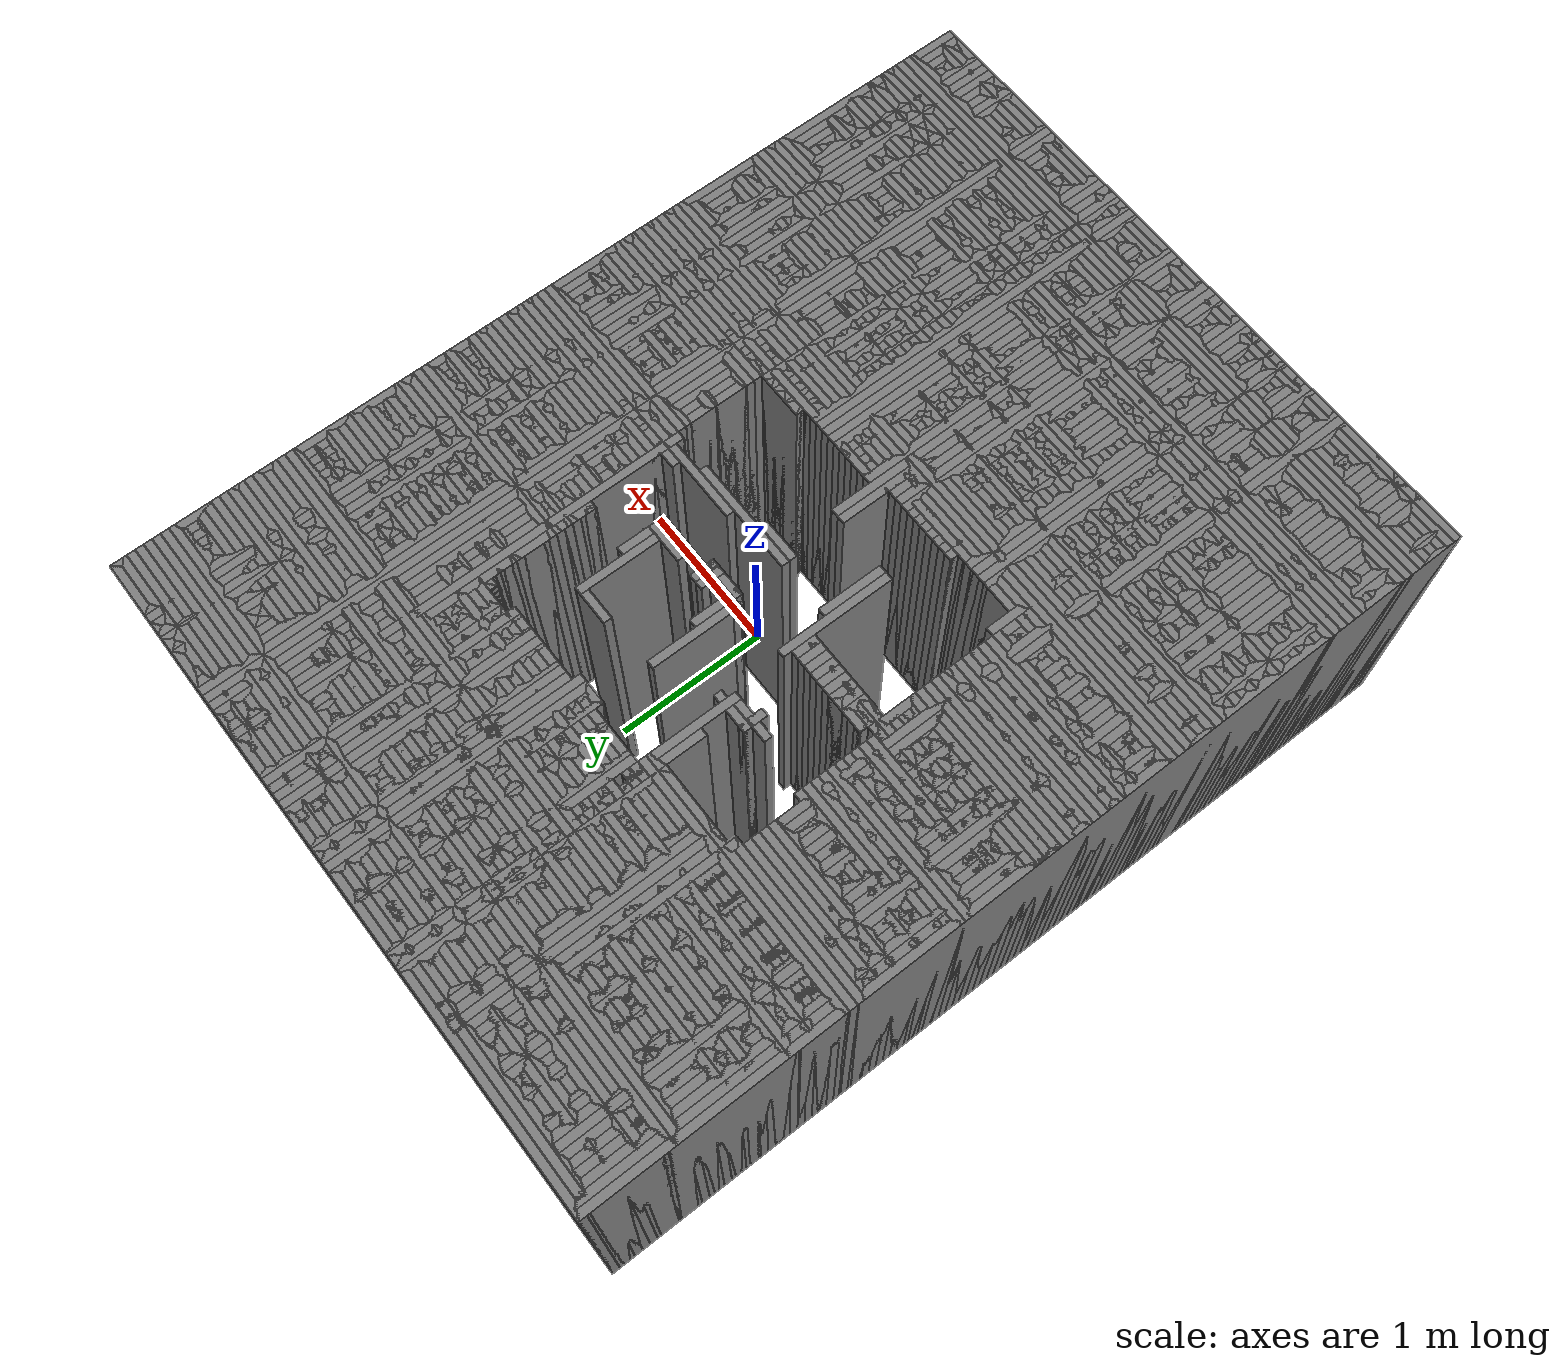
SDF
<?xml version="1.0"?>
<sdf version="1.6">
  <model name="maze_map">
    <static>true</static>

    <link name="wall_0">
      <pose>-0.41500000000000004 2.85 1.0 0 0 0</pose>
      <collision name="collision">
        <geometry>
          <box>
            <size>4.1000000000000005 0.05 2.0</size>
          </box>
        </geometry>
      </collision>
      <visual name="visual">
        <geometry>
          <box>
            <size>4.1000000000000005 0.05 2.0</size>
          </box>
        </geometry>
        <material>
          <ambient>0.3 0.3 0.3 1</ambient>
          <diffuse>0.5 0.5 0.5 1</diffuse>
        </material>
      </visual>
    </link>

    <link name="wall_1">
      <pose>-0.41500000000000004 2.8000000000000003 1.0 0 0 0</pose>
      <collision name="collision">
        <geometry>
          <box>
            <size>4.1000000000000005 0.05 2.0</size>
          </box>
        </geometry>
      </collision>
      <visual name="visual">
        <geometry>
          <box>
            <size>4.1000000000000005 0.05 2.0</size>
          </box>
        </geometry>
        <material>
          <ambient>0.3 0.3 0.3 1</ambient>
          <diffuse>0.5 0.5 0.5 1</diffuse>
        </material>
      </visual>
    </link>

    <link name="wall_2">
      <pose>-0.41500000000000004 2.7500000000000004 1.0 0 0 0</pose>
      <collision name="collision">
        <geometry>
          <box>
            <size>4.1000000000000005 0.05 2.0</size>
          </box>
        </geometry>
      </collision>
      <visual name="visual">
        <geometry>
          <box>
            <size>4.1000000000000005 0.05 2.0</size>
          </box>
        </geometry>
        <material>
          <ambient>0.3 0.3 0.3 1</ambient>
          <diffuse>0.5 0.5 0.5 1</diffuse>
        </material>
      </visual>
    </link>

    <link name="wall_3">
      <pose>-0.41500000000000004 2.7000000000000006 1.0 0 0 0</pose>
      <collision name="collision">
        <geometry>
          <box>
            <size>4.1000000000000005 0.05 2.0</size>
          </box>
        </geometry>
      </collision>
      <visual name="visual">
        <geometry>
          <box>
            <size>4.1000000000000005 0.05 2.0</size>
          </box>
        </geometry>
        <material>
          <ambient>0.3 0.3 0.3 1</ambient>
          <diffuse>0.5 0.5 0.5 1</diffuse>
        </material>
      </visual>
    </link>

    <link name="wall_4">
      <pose>-0.41500000000000004 2.650000000000001 1.0 0 0 0</pose>
      <collision name="collision">
        <geometry>
          <box>
            <size>4.1000000000000005 0.05 2.0</size>
          </box>
        </geometry>
      </collision>
      <visual name="visual">
        <geometry>
          <box>
            <size>4.1000000000000005 0.05 2.0</size>
          </box>
        </geometry>
        <material>
          <ambient>0.3 0.3 0.3 1</ambient>
          <diffuse>0.5 0.5 0.5 1</diffuse>
        </material>
      </visual>
    </link>

    <link name="wall_5">
      <pose>-0.41500000000000004 2.6 1.0 0 0 0</pose>
      <collision name="collision">
        <geometry>
          <box>
            <size>4.1000000000000005 0.05 2.0</size>
          </box>
        </geometry>
      </collision>
      <visual name="visual">
        <geometry>
          <box>
            <size>4.1000000000000005 0.05 2.0</size>
          </box>
        </geometry>
        <material>
          <ambient>0.3 0.3 0.3 1</ambient>
          <diffuse>0.5 0.5 0.5 1</diffuse>
        </material>
      </visual>
    </link>

    <link name="wall_6">
      <pose>-0.41500000000000004 2.5500000000000003 1.0 0 0 0</pose>
      <collision name="collision">
        <geometry>
          <box>
            <size>4.1000000000000005 0.05 2.0</size>
          </box>
        </geometry>
      </collision>
      <visual name="visual">
        <geometry>
          <box>
            <size>4.1000000000000005 0.05 2.0</size>
          </box>
        </geometry>
        <material>
          <ambient>0.3 0.3 0.3 1</ambient>
          <diffuse>0.5 0.5 0.5 1</diffuse>
        </material>
      </visual>
    </link>

    <link name="wall_7">
      <pose>-0.41500000000000004 2.5000000000000004 1.0 0 0 0</pose>
      <collision name="collision">
        <geometry>
          <box>
            <size>4.1000000000000005 0.05 2.0</size>
          </box>
        </geometry>
      </collision>
      <visual name="visual">
        <geometry>
          <box>
            <size>4.1000000000000005 0.05 2.0</size>
          </box>
        </geometry>
        <material>
          <ambient>0.3 0.3 0.3 1</ambient>
          <diffuse>0.5 0.5 0.5 1</diffuse>
        </material>
      </visual>
    </link>

    <link name="wall_8">
      <pose>-0.41500000000000004 2.4500000000000006 1.0 0 0 0</pose>
      <collision name="collision">
        <geometry>
          <box>
            <size>4.1000000000000005 0.05 2.0</size>
          </box>
        </geometry>
      </collision>
      <visual name="visual">
        <geometry>
          <box>
            <size>4.1000000000000005 0.05 2.0</size>
          </box>
        </geometry>
        <material>
          <ambient>0.3 0.3 0.3 1</ambient>
          <diffuse>0.5 0.5 0.5 1</diffuse>
        </material>
      </visual>
    </link>

    <link name="wall_9">
      <pose>-0.41500000000000004 2.400000000000001 1.0 0 0 0</pose>
      <collision name="collision">
        <geometry>
          <box>
            <size>4.1000000000000005 0.05 2.0</size>
          </box>
        </geometry>
      </collision>
      <visual name="visual">
        <geometry>
          <box>
            <size>4.1000000000000005 0.05 2.0</size>
          </box>
        </geometry>
        <material>
          <ambient>0.3 0.3 0.3 1</ambient>
          <diffuse>0.5 0.5 0.5 1</diffuse>
        </material>
      </visual>
    </link>

    <link name="wall_10">
      <pose>-0.41500000000000004 2.35 1.0 0 0 0</pose>
      <collision name="collision">
        <geometry>
          <box>
            <size>4.1000000000000005 0.05 2.0</size>
          </box>
        </geometry>
      </collision>
      <visual name="visual">
        <geometry>
          <box>
            <size>4.1000000000000005 0.05 2.0</size>
          </box>
        </geometry>
        <material>
          <ambient>0.3 0.3 0.3 1</ambient>
          <diffuse>0.5 0.5 0.5 1</diffuse>
        </material>
      </visual>
    </link>

    <link name="wall_11">
      <pose>-0.41500000000000004 2.3000000000000003 1.0 0 0 0</pose>
      <collision name="collision">
        <geometry>
          <box>
            <size>4.1000000000000005 0.05 2.0</size>
          </box>
        </geometry>
      </collision>
      <visual name="visual">
        <geometry>
          <box>
            <size>4.1000000000000005 0.05 2.0</size>
          </box>
        </geometry>
        <material>
          <ambient>0.3 0.3 0.3 1</ambient>
          <diffuse>0.5 0.5 0.5 1</diffuse>
        </material>
      </visual>
    </link>

    <link name="wall_12">
      <pose>-0.41500000000000004 2.2500000000000004 1.0 0 0 0</pose>
      <collision name="collision">
        <geometry>
          <box>
            <size>4.1000000000000005 0.05 2.0</size>
          </box>
        </geometry>
      </collision>
      <visual name="visual">
        <geometry>
          <box>
            <size>4.1000000000000005 0.05 2.0</size>
          </box>
        </geometry>
        <material>
          <ambient>0.3 0.3 0.3 1</ambient>
          <diffuse>0.5 0.5 0.5 1</diffuse>
        </material>
      </visual>
    </link>

    <link name="wall_13">
      <pose>-0.41500000000000004 2.2000000000000006 1.0 0 0 0</pose>
      <collision name="collision">
        <geometry>
          <box>
            <size>4.1000000000000005 0.05 2.0</size>
          </box>
        </geometry>
      </collision>
      <visual name="visual">
        <geometry>
          <box>
            <size>4.1000000000000005 0.05 2.0</size>
          </box>
        </geometry>
        <material>
          <ambient>0.3 0.3 0.3 1</ambient>
          <diffuse>0.5 0.5 0.5 1</diffuse>
        </material>
      </visual>
    </link>

    <link name="wall_14">
      <pose>-0.41500000000000004 2.150000000000001 1.0 0 0 0</pose>
      <collision name="collision">
        <geometry>
          <box>
            <size>4.1000000000000005 0.05 2.0</size>
          </box>
        </geometry>
      </collision>
      <visual name="visual">
        <geometry>
          <box>
            <size>4.1000000000000005 0.05 2.0</size>
          </box>
        </geometry>
        <material>
          <ambient>0.3 0.3 0.3 1</ambient>
          <diffuse>0.5 0.5 0.5 1</diffuse>
        </material>
      </visual>
    </link>

    <link name="wall_15">
      <pose>-0.41500000000000004 2.1 1.0 0 0 0</pose>
      <collision name="collision">
        <geometry>
          <box>
            <size>4.1000000000000005 0.05 2.0</size>
          </box>
        </geometry>
      </collision>
      <visual name="visual">
        <geometry>
          <box>
            <size>4.1000000000000005 0.05 2.0</size>
          </box>
        </geometry>
        <material>
          <ambient>0.3 0.3 0.3 1</ambient>
          <diffuse>0.5 0.5 0.5 1</diffuse>
        </material>
      </visual>
    </link>

    <link name="wall_16">
      <pose>-0.41500000000000004 2.0500000000000003 1.0 0 0 0</pose>
      <collision name="collision">
        <geometry>
          <box>
            <size>4.1000000000000005 0.05 2.0</size>
          </box>
        </geometry>
      </collision>
      <visual name="visual">
        <geometry>
          <box>
            <size>4.1000000000000005 0.05 2.0</size>
          </box>
        </geometry>
        <material>
          <ambient>0.3 0.3 0.3 1</ambient>
          <diffuse>0.5 0.5 0.5 1</diffuse>
        </material>
      </visual>
    </link>

    <link name="wall_17">
      <pose>-0.41500000000000004 2.0000000000000004 1.0 0 0 0</pose>
      <collision name="collision">
        <geometry>
          <box>
            <size>4.1000000000000005 0.05 2.0</size>
          </box>
        </geometry>
      </collision>
      <visual name="visual">
        <geometry>
          <box>
            <size>4.1000000000000005 0.05 2.0</size>
          </box>
        </geometry>
        <material>
          <ambient>0.3 0.3 0.3 1</ambient>
          <diffuse>0.5 0.5 0.5 1</diffuse>
        </material>
      </visual>
    </link>

    <link name="wall_18">
      <pose>-0.41500000000000004 1.9500000000000006 1.0 0 0 0</pose>
      <collision name="collision">
        <geometry>
          <box>
            <size>4.1000000000000005 0.05 2.0</size>
          </box>
        </geometry>
      </collision>
      <visual name="visual">
        <geometry>
          <box>
            <size>4.1000000000000005 0.05 2.0</size>
          </box>
        </geometry>
        <material>
          <ambient>0.3 0.3 0.3 1</ambient>
          <diffuse>0.5 0.5 0.5 1</diffuse>
        </material>
      </visual>
    </link>

    <link name="wall_19">
      <pose>-0.41500000000000004 1.9 1.0 0 0 0</pose>
      <collision name="collision">
        <geometry>
          <box>
            <size>4.1000000000000005 0.05 2.0</size>
          </box>
        </geometry>
      </collision>
      <visual name="visual">
        <geometry>
          <box>
            <size>4.1000000000000005 0.05 2.0</size>
          </box>
        </geometry>
        <material>
          <ambient>0.3 0.3 0.3 1</ambient>
          <diffuse>0.5 0.5 0.5 1</diffuse>
        </material>
      </visual>
    </link>

    <link name="wall_20">
      <pose>-0.41500000000000004 1.85 1.0 0 0 0</pose>
      <collision name="collision">
        <geometry>
          <box>
            <size>4.1000000000000005 0.05 2.0</size>
          </box>
        </geometry>
      </collision>
      <visual name="visual">
        <geometry>
          <box>
            <size>4.1000000000000005 0.05 2.0</size>
          </box>
        </geometry>
        <material>
          <ambient>0.3 0.3 0.3 1</ambient>
          <diffuse>0.5 0.5 0.5 1</diffuse>
        </material>
      </visual>
    </link>

    <link name="wall_21">
      <pose>-0.41500000000000004 1.8000000000000003 1.0 0 0 0</pose>
      <collision name="collision">
        <geometry>
          <box>
            <size>4.1000000000000005 0.05 2.0</size>
          </box>
        </geometry>
      </collision>
      <visual name="visual">
        <geometry>
          <box>
            <size>4.1000000000000005 0.05 2.0</size>
          </box>
        </geometry>
        <material>
          <ambient>0.3 0.3 0.3 1</ambient>
          <diffuse>0.5 0.5 0.5 1</diffuse>
        </material>
      </visual>
    </link>

    <link name="wall_22">
      <pose>-0.41500000000000004 1.7500000000000004 1.0 0 0 0</pose>
      <collision name="collision">
        <geometry>
          <box>
            <size>4.1000000000000005 0.05 2.0</size>
          </box>
        </geometry>
      </collision>
      <visual name="visual">
        <geometry>
          <box>
            <size>4.1000000000000005 0.05 2.0</size>
          </box>
        </geometry>
        <material>
          <ambient>0.3 0.3 0.3 1</ambient>
          <diffuse>0.5 0.5 0.5 1</diffuse>
        </material>
      </visual>
    </link>

    <link name="wall_23">
      <pose>-0.41500000000000004 1.7000000000000006 1.0 0 0 0</pose>
      <collision name="collision">
        <geometry>
          <box>
            <size>4.1000000000000005 0.05 2.0</size>
          </box>
        </geometry>
      </collision>
      <visual name="visual">
        <geometry>
          <box>
            <size>4.1000000000000005 0.05 2.0</size>
          </box>
        </geometry>
        <material>
          <ambient>0.3 0.3 0.3 1</ambient>
          <diffuse>0.5 0.5 0.5 1</diffuse>
        </material>
      </visual>
    </link>

    <link name="wall_24">
      <pose>-0.41500000000000004 1.65 1.0 0 0 0</pose>
      <collision name="collision">
        <geometry>
          <box>
            <size>4.1000000000000005 0.05 2.0</size>
          </box>
        </geometry>
      </collision>
      <visual name="visual">
        <geometry>
          <box>
            <size>4.1000000000000005 0.05 2.0</size>
          </box>
        </geometry>
        <material>
          <ambient>0.3 0.3 0.3 1</ambient>
          <diffuse>0.5 0.5 0.5 1</diffuse>
        </material>
      </visual>
    </link>

    <link name="wall_25">
      <pose>-0.41500000000000004 1.6 1.0 0 0 0</pose>
      <collision name="collision">
        <geometry>
          <box>
            <size>4.1000000000000005 0.05 2.0</size>
          </box>
        </geometry>
      </collision>
      <visual name="visual">
        <geometry>
          <box>
            <size>4.1000000000000005 0.05 2.0</size>
          </box>
        </geometry>
        <material>
          <ambient>0.3 0.3 0.3 1</ambient>
          <diffuse>0.5 0.5 0.5 1</diffuse>
        </material>
      </visual>
    </link>

    <link name="wall_26">
      <pose>-0.41500000000000004 1.5500000000000003 1.0 0 0 0</pose>
      <collision name="collision">
        <geometry>
          <box>
            <size>4.1000000000000005 0.05 2.0</size>
          </box>
        </geometry>
      </collision>
      <visual name="visual">
        <geometry>
          <box>
            <size>4.1000000000000005 0.05 2.0</size>
          </box>
        </geometry>
        <material>
          <ambient>0.3 0.3 0.3 1</ambient>
          <diffuse>0.5 0.5 0.5 1</diffuse>
        </material>
      </visual>
    </link>

    <link name="wall_27">
      <pose>-1.69 1.5000000000000004 1.0 0 0 0</pose>
      <collision name="collision">
        <geometry>
          <box>
            <size>1.55 0.05 2.0</size>
          </box>
        </geometry>
      </collision>
      <visual name="visual">
        <geometry>
          <box>
            <size>1.55 0.05 2.0</size>
          </box>
        </geometry>
        <material>
          <ambient>0.3 0.3 0.3 1</ambient>
          <diffuse>0.5 0.5 0.5 1</diffuse>
        </material>
      </visual>
    </link>

    <link name="wall_28">
      <pose>0.38500000000000023 1.5000000000000004 1.0 0 0 0</pose>
      <collision name="collision">
        <geometry>
          <box>
            <size>2.5 0.05 2.0</size>
          </box>
        </geometry>
      </collision>
      <visual name="visual">
        <geometry>
          <box>
            <size>2.5 0.05 2.0</size>
          </box>
        </geometry>
        <material>
          <ambient>0.3 0.3 0.3 1</ambient>
          <diffuse>0.5 0.5 0.5 1</diffuse>
        </material>
      </visual>
    </link>

    <link name="wall_29">
      <pose>-0.41500000000000004 1.4500000000000006 1.0 0 0 0</pose>
      <collision name="collision">
        <geometry>
          <box>
            <size>4.1000000000000005 0.05 2.0</size>
          </box>
        </geometry>
      </collision>
      <visual name="visual">
        <geometry>
          <box>
            <size>4.1000000000000005 0.05 2.0</size>
          </box>
        </geometry>
        <material>
          <ambient>0.3 0.3 0.3 1</ambient>
          <diffuse>0.5 0.5 0.5 1</diffuse>
        </material>
      </visual>
    </link>

    <link name="wall_30">
      <pose>-1.14 1.4 1.0 0 0 0</pose>
      <collision name="collision">
        <geometry>
          <box>
            <size>2.6500000000000004 0.05 2.0</size>
          </box>
        </geometry>
      </collision>
      <visual name="visual">
        <geometry>
          <box>
            <size>2.6500000000000004 0.05 2.0</size>
          </box>
        </geometry>
        <material>
          <ambient>0.3 0.3 0.3 1</ambient>
          <diffuse>0.5 0.5 0.5 1</diffuse>
        </material>
      </visual>
    </link>

    <link name="wall_31">
      <pose>0.9850000000000003 1.4 1.0 0 0 0</pose>
      <collision name="collision">
        <geometry>
          <box>
            <size>1.3 0.05 2.0</size>
          </box>
        </geometry>
      </collision>
      <visual name="visual">
        <geometry>
          <box>
            <size>1.3 0.05 2.0</size>
          </box>
        </geometry>
        <material>
          <ambient>0.3 0.3 0.3 1</ambient>
          <diffuse>0.5 0.5 0.5 1</diffuse>
        </material>
      </visual>
    </link>

    <link name="wall_32">
      <pose>-1.665 1.35 1.0 0 0 0</pose>
      <collision name="collision">
        <geometry>
          <box>
            <size>1.6 0.05 2.0</size>
          </box>
        </geometry>
      </collision>
      <visual name="visual">
        <geometry>
          <box>
            <size>1.6 0.05 2.0</size>
          </box>
        </geometry>
        <material>
          <ambient>0.3 0.3 0.3 1</ambient>
          <diffuse>0.5 0.5 0.5 1</diffuse>
        </material>
      </visual>
    </link>

    <link name="wall_33">
      <pose>-0.41500000000000004 1.35 1.0 0 0 0</pose>
      <collision name="collision">
        <geometry>
          <box>
            <size>0.2 0.05 2.0</size>
          </box>
        </geometry>
      </collision>
      <visual name="visual">
        <geometry>
          <box>
            <size>0.2 0.05 2.0</size>
          </box>
        </geometry>
        <material>
          <ambient>0.3 0.3 0.3 1</ambient>
          <diffuse>0.5 0.5 0.5 1</diffuse>
        </material>
      </visual>
    </link>

    <link name="wall_34">
      <pose>1.0100000000000002 1.35 1.0 0 0 0</pose>
      <collision name="collision">
        <geometry>
          <box>
            <size>1.25 0.05 2.0</size>
          </box>
        </geometry>
      </collision>
      <visual name="visual">
        <geometry>
          <box>
            <size>1.25 0.05 2.0</size>
          </box>
        </geometry>
        <material>
          <ambient>0.3 0.3 0.3 1</ambient>
          <diffuse>0.5 0.5 0.5 1</diffuse>
        </material>
      </visual>
    </link>

    <link name="wall_35">
      <pose>-1.665 1.3000000000000003 1.0 0 0 0</pose>
      <collision name="collision">
        <geometry>
          <box>
            <size>1.6 0.05 2.0</size>
          </box>
        </geometry>
      </collision>
      <visual name="visual">
        <geometry>
          <box>
            <size>1.6 0.05 2.0</size>
          </box>
        </geometry>
        <material>
          <ambient>0.3 0.3 0.3 1</ambient>
          <diffuse>0.5 0.5 0.5 1</diffuse>
        </material>
      </visual>
    </link>

    <link name="wall_36">
      <pose>1.0100000000000002 1.3000000000000003 1.0 0 0 0</pose>
      <collision name="collision">
        <geometry>
          <box>
            <size>1.25 0.05 2.0</size>
          </box>
        </geometry>
      </collision>
      <visual name="visual">
        <geometry>
          <box>
            <size>1.25 0.05 2.0</size>
          </box>
        </geometry>
        <material>
          <ambient>0.3 0.3 0.3 1</ambient>
          <diffuse>0.5 0.5 0.5 1</diffuse>
        </material>
      </visual>
    </link>

    <link name="wall_37">
      <pose>-1.9649999999999999 1.2500000000000004 1.0 0 0 0</pose>
      <collision name="collision">
        <geometry>
          <box>
            <size>1.0 0.05 2.0</size>
          </box>
        </geometry>
      </collision>
      <visual name="visual">
        <geometry>
          <box>
            <size>1.0 0.05 2.0</size>
          </box>
        </geometry>
        <material>
          <ambient>0.3 0.3 0.3 1</ambient>
          <diffuse>0.5 0.5 0.5 1</diffuse>
        </material>
      </visual>
    </link>

    <link name="wall_38">
      <pose>1.0100000000000002 1.2500000000000004 1.0 0 0 0</pose>
      <collision name="collision">
        <geometry>
          <box>
            <size>1.25 0.05 2.0</size>
          </box>
        </geometry>
      </collision>
      <visual name="visual">
        <geometry>
          <box>
            <size>1.25 0.05 2.0</size>
          </box>
        </geometry>
        <material>
          <ambient>0.3 0.3 0.3 1</ambient>
          <diffuse>0.5 0.5 0.5 1</diffuse>
        </material>
      </visual>
    </link>

    <link name="wall_39">
      <pose>-1.99 1.2000000000000002 1.0 0 0 0</pose>
      <collision name="collision">
        <geometry>
          <box>
            <size>0.9500000000000001 0.05 2.0</size>
          </box>
        </geometry>
      </collision>
      <visual name="visual">
        <geometry>
          <box>
            <size>0.9500000000000001 0.05 2.0</size>
          </box>
        </geometry>
        <material>
          <ambient>0.3 0.3 0.3 1</ambient>
          <diffuse>0.5 0.5 0.5 1</diffuse>
        </material>
      </visual>
    </link>

    <link name="wall_40">
      <pose>1.0100000000000002 1.2000000000000002 1.0 0 0 0</pose>
      <collision name="collision">
        <geometry>
          <box>
            <size>1.25 0.05 2.0</size>
          </box>
        </geometry>
      </collision>
      <visual name="visual">
        <geometry>
          <box>
            <size>1.25 0.05 2.0</size>
          </box>
        </geometry>
        <material>
          <ambient>0.3 0.3 0.3 1</ambient>
          <diffuse>0.5 0.5 0.5 1</diffuse>
        </material>
      </visual>
    </link>

    <link name="wall_41">
      <pose>-1.99 1.1500000000000004 1.0 0 0 0</pose>
      <collision name="collision">
        <geometry>
          <box>
            <size>0.9500000000000001 0.05 2.0</size>
          </box>
        </geometry>
      </collision>
      <visual name="visual">
        <geometry>
          <box>
            <size>0.9500000000000001 0.05 2.0</size>
          </box>
        </geometry>
        <material>
          <ambient>0.3 0.3 0.3 1</ambient>
          <diffuse>0.5 0.5 0.5 1</diffuse>
        </material>
      </visual>
    </link>

    <link name="wall_42">
      <pose>1.0100000000000002 1.1500000000000004 1.0 0 0 0</pose>
      <collision name="collision">
        <geometry>
          <box>
            <size>1.25 0.05 2.0</size>
          </box>
        </geometry>
      </collision>
      <visual name="visual">
        <geometry>
          <box>
            <size>1.25 0.05 2.0</size>
          </box>
        </geometry>
        <material>
          <ambient>0.3 0.3 0.3 1</ambient>
          <diffuse>0.5 0.5 0.5 1</diffuse>
        </material>
      </visual>
    </link>

    <link name="wall_43">
      <pose>-1.99 1.1 1.0 0 0 0</pose>
      <collision name="collision">
        <geometry>
          <box>
            <size>0.9500000000000001 0.05 2.0</size>
          </box>
        </geometry>
      </collision>
      <visual name="visual">
        <geometry>
          <box>
            <size>0.9500000000000001 0.05 2.0</size>
          </box>
        </geometry>
        <material>
          <ambient>0.3 0.3 0.3 1</ambient>
          <diffuse>0.5 0.5 0.5 1</diffuse>
        </material>
      </visual>
    </link>

    <link name="wall_44">
      <pose>1.0100000000000002 1.1 1.0 0 0 0</pose>
      <collision name="collision">
        <geometry>
          <box>
            <size>1.25 0.05 2.0</size>
          </box>
        </geometry>
      </collision>
      <visual name="visual">
        <geometry>
          <box>
            <size>1.25 0.05 2.0</size>
          </box>
        </geometry>
        <material>
          <ambient>0.3 0.3 0.3 1</ambient>
          <diffuse>0.5 0.5 0.5 1</diffuse>
        </material>
      </visual>
    </link>

    <link name="wall_45">
      <pose>-1.99 1.0500000000000003 1.0 0 0 0</pose>
      <collision name="collision">
        <geometry>
          <box>
            <size>0.9500000000000001 0.05 2.0</size>
          </box>
        </geometry>
      </collision>
      <visual name="visual">
        <geometry>
          <box>
            <size>0.9500000000000001 0.05 2.0</size>
          </box>
        </geometry>
        <material>
          <ambient>0.3 0.3 0.3 1</ambient>
          <diffuse>0.5 0.5 0.5 1</diffuse>
        </material>
      </visual>
    </link>

    <link name="wall_46">
      <pose>-0.03999999999999959 1.0500000000000003 1.0 0 0 0</pose>
      <collision name="collision">
        <geometry>
          <box>
            <size>0.25 0.05 2.0</size>
          </box>
        </geometry>
      </collision>
      <visual name="visual">
        <geometry>
          <box>
            <size>0.25 0.05 2.0</size>
          </box>
        </geometry>
        <material>
          <ambient>0.3 0.3 0.3 1</ambient>
          <diffuse>0.5 0.5 0.5 1</diffuse>
        </material>
      </visual>
    </link>

    <link name="wall_47">
      <pose>1.0100000000000002 1.0500000000000003 1.0 0 0 0</pose>
      <collision name="collision">
        <geometry>
          <box>
            <size>1.25 0.05 2.0</size>
          </box>
        </geometry>
      </collision>
      <visual name="visual">
        <geometry>
          <box>
            <size>1.25 0.05 2.0</size>
          </box>
        </geometry>
        <material>
          <ambient>0.3 0.3 0.3 1</ambient>
          <diffuse>0.5 0.5 0.5 1</diffuse>
        </material>
      </visual>
    </link>

    <link name="wall_48">
      <pose>-1.99 1.0000000000000004 1.0 0 0 0</pose>
      <collision name="collision">
        <geometry>
          <box>
            <size>0.9500000000000001 0.05 2.0</size>
          </box>
        </geometry>
      </collision>
      <visual name="visual">
        <geometry>
          <box>
            <size>0.9500000000000001 0.05 2.0</size>
          </box>
        </geometry>
        <material>
          <ambient>0.3 0.3 0.3 1</ambient>
          <diffuse>0.5 0.5 0.5 1</diffuse>
        </material>
      </visual>
    </link>

    <link name="wall_49">
      <pose>1.0100000000000002 1.0000000000000004 1.0 0 0 0</pose>
      <collision name="collision">
        <geometry>
          <box>
            <size>1.25 0.05 2.0</size>
          </box>
        </geometry>
      </collision>
      <visual name="visual">
        <geometry>
          <box>
            <size>1.25 0.05 2.0</size>
          </box>
        </geometry>
        <material>
          <ambient>0.3 0.3 0.3 1</ambient>
          <diffuse>0.5 0.5 0.5 1</diffuse>
        </material>
      </visual>
    </link>

    <link name="wall_50">
      <pose>-1.99 0.9500000000000002 1.0 0 0 0</pose>
      <collision name="collision">
        <geometry>
          <box>
            <size>0.9500000000000001 0.05 2.0</size>
          </box>
        </geometry>
      </collision>
      <visual name="visual">
        <geometry>
          <box>
            <size>0.9500000000000001 0.05 2.0</size>
          </box>
        </geometry>
        <material>
          <ambient>0.3 0.3 0.3 1</ambient>
          <diffuse>0.5 0.5 0.5 1</diffuse>
        </material>
      </visual>
    </link>

    <link name="wall_51">
      <pose>1.0100000000000002 0.9500000000000002 1.0 0 0 0</pose>
      <collision name="collision">
        <geometry>
          <box>
            <size>1.25 0.05 2.0</size>
          </box>
        </geometry>
      </collision>
      <visual name="visual">
        <geometry>
          <box>
            <size>1.25 0.05 2.0</size>
          </box>
        </geometry>
        <material>
          <ambient>0.3 0.3 0.3 1</ambient>
          <diffuse>0.5 0.5 0.5 1</diffuse>
        </material>
      </visual>
    </link>

    <link name="wall_52">
      <pose>-1.99 0.9000000000000004 1.0 0 0 0</pose>
      <collision name="collision">
        <geometry>
          <box>
            <size>0.9500000000000001 0.05 2.0</size>
          </box>
        </geometry>
      </collision>
      <visual name="visual">
        <geometry>
          <box>
            <size>0.9500000000000001 0.05 2.0</size>
          </box>
        </geometry>
        <material>
          <ambient>0.3 0.3 0.3 1</ambient>
          <diffuse>0.5 0.5 0.5 1</diffuse>
        </material>
      </visual>
    </link>

    <link name="wall_53">
      <pose>1.0100000000000002 0.9000000000000004 1.0 0 0 0</pose>
      <collision name="collision">
        <geometry>
          <box>
            <size>1.25 0.05 2.0</size>
          </box>
        </geometry>
      </collision>
      <visual name="visual">
        <geometry>
          <box>
            <size>1.25 0.05 2.0</size>
          </box>
        </geometry>
        <material>
          <ambient>0.3 0.3 0.3 1</ambient>
          <diffuse>0.5 0.5 0.5 1</diffuse>
        </material>
      </visual>
    </link>

    <link name="wall_54">
      <pose>-1.9649999999999999 0.8500000000000001 1.0 0 0 0</pose>
      <collision name="collision">
        <geometry>
          <box>
            <size>1.0 0.05 2.0</size>
          </box>
        </geometry>
      </collision>
      <visual name="visual">
        <geometry>
          <box>
            <size>1.0 0.05 2.0</size>
          </box>
        </geometry>
        <material>
          <ambient>0.3 0.3 0.3 1</ambient>
          <diffuse>0.5 0.5 0.5 1</diffuse>
        </material>
      </visual>
    </link>

    <link name="wall_55">
      <pose>-0.94 0.8500000000000001 1.0 0 0 0</pose>
      <collision name="collision">
        <geometry>
          <box>
            <size>0.25 0.05 2.0</size>
          </box>
        </geometry>
      </collision>
      <visual name="visual">
        <geometry>
          <box>
            <size>0.25 0.05 2.0</size>
          </box>
        </geometry>
        <material>
          <ambient>0.3 0.3 0.3 1</ambient>
          <diffuse>0.5 0.5 0.5 1</diffuse>
        </material>
      </visual>
    </link>

    <link name="wall_56">
      <pose>1.0100000000000002 0.8500000000000001 1.0 0 0 0</pose>
      <collision name="collision">
        <geometry>
          <box>
            <size>1.25 0.05 2.0</size>
          </box>
        </geometry>
      </collision>
      <visual name="visual">
        <geometry>
          <box>
            <size>1.25 0.05 2.0</size>
          </box>
        </geometry>
        <material>
          <ambient>0.3 0.3 0.3 1</ambient>
          <diffuse>0.5 0.5 0.5 1</diffuse>
        </material>
      </visual>
    </link>

    <link name="wall_57">
      <pose>-1.9649999999999999 0.8000000000000003 1.0 0 0 0</pose>
      <collision name="collision">
        <geometry>
          <box>
            <size>1.0 0.05 2.0</size>
          </box>
        </geometry>
      </collision>
      <visual name="visual">
        <geometry>
          <box>
            <size>1.0 0.05 2.0</size>
          </box>
        </geometry>
        <material>
          <ambient>0.3 0.3 0.3 1</ambient>
          <diffuse>0.5 0.5 0.5 1</diffuse>
        </material>
      </visual>
    </link>

    <link name="wall_58">
      <pose>-1.015 0.8000000000000003 1.0 0 0 0</pose>
      <collision name="collision">
        <geometry>
          <box>
            <size>0.30000000000000004 0.05 2.0</size>
          </box>
        </geometry>
      </collision>
      <visual name="visual">
        <geometry>
          <box>
            <size>0.30000000000000004 0.05 2.0</size>
          </box>
        </geometry>
        <material>
          <ambient>0.3 0.3 0.3 1</ambient>
          <diffuse>0.5 0.5 0.5 1</diffuse>
        </material>
      </visual>
    </link>

    <link name="wall_59">
      <pose>1.0100000000000002 0.8000000000000003 1.0 0 0 0</pose>
      <collision name="collision">
        <geometry>
          <box>
            <size>1.25 0.05 2.0</size>
          </box>
        </geometry>
      </collision>
      <visual name="visual">
        <geometry>
          <box>
            <size>1.25 0.05 2.0</size>
          </box>
        </geometry>
        <material>
          <ambient>0.3 0.3 0.3 1</ambient>
          <diffuse>0.5 0.5 0.5 1</diffuse>
        </material>
      </visual>
    </link>

    <link name="wall_60">
      <pose>-1.9649999999999999 0.7500000000000004 1.0 0 0 0</pose>
      <collision name="collision">
        <geometry>
          <box>
            <size>1.0 0.05 2.0</size>
          </box>
        </geometry>
      </collision>
      <visual name="visual">
        <geometry>
          <box>
            <size>1.0 0.05 2.0</size>
          </box>
        </geometry>
        <material>
          <ambient>0.3 0.3 0.3 1</ambient>
          <diffuse>0.5 0.5 0.5 1</diffuse>
        </material>
      </visual>
    </link>

    <link name="wall_61">
      <pose>1.0100000000000002 0.7500000000000004 1.0 0 0 0</pose>
      <collision name="collision">
        <geometry>
          <box>
            <size>1.25 0.05 2.0</size>
          </box>
        </geometry>
      </collision>
      <visual name="visual">
        <geometry>
          <box>
            <size>1.25 0.05 2.0</size>
          </box>
        </geometry>
        <material>
          <ambient>0.3 0.3 0.3 1</ambient>
          <diffuse>0.5 0.5 0.5 1</diffuse>
        </material>
      </visual>
    </link>

    <link name="wall_62">
      <pose>-1.9649999999999999 0.7000000000000002 1.0 0 0 0</pose>
      <collision name="collision">
        <geometry>
          <box>
            <size>1.0 0.05 2.0</size>
          </box>
        </geometry>
      </collision>
      <visual name="visual">
        <geometry>
          <box>
            <size>1.0 0.05 2.0</size>
          </box>
        </geometry>
        <material>
          <ambient>0.3 0.3 0.3 1</ambient>
          <diffuse>0.5 0.5 0.5 1</diffuse>
        </material>
      </visual>
    </link>

    <link name="wall_63">
      <pose>1.0350000000000001 0.7000000000000002 1.0 0 0 0</pose>
      <collision name="collision">
        <geometry>
          <box>
            <size>1.2000000000000002 0.05 2.0</size>
          </box>
        </geometry>
      </collision>
      <visual name="visual">
        <geometry>
          <box>
            <size>1.2000000000000002 0.05 2.0</size>
          </box>
        </geometry>
        <material>
          <ambient>0.3 0.3 0.3 1</ambient>
          <diffuse>0.5 0.5 0.5 1</diffuse>
        </material>
      </visual>
    </link>

    <link name="wall_64">
      <pose>-1.9649999999999999 0.6500000000000004 1.0 0 0 0</pose>
      <collision name="collision">
        <geometry>
          <box>
            <size>1.0 0.05 2.0</size>
          </box>
        </geometry>
      </collision>
      <visual name="visual">
        <geometry>
          <box>
            <size>1.0 0.05 2.0</size>
          </box>
        </geometry>
        <material>
          <ambient>0.3 0.3 0.3 1</ambient>
          <diffuse>0.5 0.5 0.5 1</diffuse>
        </material>
      </visual>
    </link>

    <link name="wall_65">
      <pose>1.0350000000000001 0.6500000000000004 1.0 0 0 0</pose>
      <collision name="collision">
        <geometry>
          <box>
            <size>1.2000000000000002 0.05 2.0</size>
          </box>
        </geometry>
      </collision>
      <visual name="visual">
        <geometry>
          <box>
            <size>1.2000000000000002 0.05 2.0</size>
          </box>
        </geometry>
        <material>
          <ambient>0.3 0.3 0.3 1</ambient>
          <diffuse>0.5 0.5 0.5 1</diffuse>
        </material>
      </visual>
    </link>

    <link name="wall_66">
      <pose>-1.9649999999999999 0.6000000000000001 1.0 0 0 0</pose>
      <collision name="collision">
        <geometry>
          <box>
            <size>1.0 0.05 2.0</size>
          </box>
        </geometry>
      </collision>
      <visual name="visual">
        <geometry>
          <box>
            <size>1.0 0.05 2.0</size>
          </box>
        </geometry>
        <material>
          <ambient>0.3 0.3 0.3 1</ambient>
          <diffuse>0.5 0.5 0.5 1</diffuse>
        </material>
      </visual>
    </link>

    <link name="wall_67">
      <pose>1.0350000000000001 0.6000000000000001 1.0 0 0 0</pose>
      <collision name="collision">
        <geometry>
          <box>
            <size>1.2000000000000002 0.05 2.0</size>
          </box>
        </geometry>
      </collision>
      <visual name="visual">
        <geometry>
          <box>
            <size>1.2000000000000002 0.05 2.0</size>
          </box>
        </geometry>
        <material>
          <ambient>0.3 0.3 0.3 1</ambient>
          <diffuse>0.5 0.5 0.5 1</diffuse>
        </material>
      </visual>
    </link>

    <link name="wall_68">
      <pose>-1.9649999999999999 0.5500000000000003 1.0 0 0 0</pose>
      <collision name="collision">
        <geometry>
          <box>
            <size>1.0 0.05 2.0</size>
          </box>
        </geometry>
      </collision>
      <visual name="visual">
        <geometry>
          <box>
            <size>1.0 0.05 2.0</size>
          </box>
        </geometry>
        <material>
          <ambient>0.3 0.3 0.3 1</ambient>
          <diffuse>0.5 0.5 0.5 1</diffuse>
        </material>
      </visual>
    </link>

    <link name="wall_69">
      <pose>0.010000000000000231 0.5500000000000003 1.0 0 0 0</pose>
      <collision name="collision">
        <geometry>
          <box>
            <size>0.25 0.05 2.0</size>
          </box>
        </geometry>
      </collision>
      <visual name="visual">
        <geometry>
          <box>
            <size>0.25 0.05 2.0</size>
          </box>
        </geometry>
        <material>
          <ambient>0.3 0.3 0.3 1</ambient>
          <diffuse>0.5 0.5 0.5 1</diffuse>
        </material>
      </visual>
    </link>

    <link name="wall_70">
      <pose>1.0350000000000001 0.5500000000000003 1.0 0 0 0</pose>
      <collision name="collision">
        <geometry>
          <box>
            <size>1.2000000000000002 0.05 2.0</size>
          </box>
        </geometry>
      </collision>
      <visual name="visual">
        <geometry>
          <box>
            <size>1.2000000000000002 0.05 2.0</size>
          </box>
        </geometry>
        <material>
          <ambient>0.3 0.3 0.3 1</ambient>
          <diffuse>0.5 0.5 0.5 1</diffuse>
        </material>
      </visual>
    </link>

    <link name="wall_71">
      <pose>-1.9649999999999999 0.5000000000000004 1.0 0 0 0</pose>
      <collision name="collision">
        <geometry>
          <box>
            <size>1.0 0.05 2.0</size>
          </box>
        </geometry>
      </collision>
      <visual name="visual">
        <geometry>
          <box>
            <size>1.0 0.05 2.0</size>
          </box>
        </geometry>
        <material>
          <ambient>0.3 0.3 0.3 1</ambient>
          <diffuse>0.5 0.5 0.5 1</diffuse>
        </material>
      </visual>
    </link>

    <link name="wall_72">
      <pose>-0.18999999999999995 0.5000000000000004 1.0 0 0 0</pose>
      <collision name="collision">
        <geometry>
          <box>
            <size>0.65 0.05 2.0</size>
          </box>
        </geometry>
      </collision>
      <visual name="visual">
        <geometry>
          <box>
            <size>0.65 0.05 2.0</size>
          </box>
        </geometry>
        <material>
          <ambient>0.3 0.3 0.3 1</ambient>
          <diffuse>0.5 0.5 0.5 1</diffuse>
        </material>
      </visual>
    </link>

    <link name="wall_73">
      <pose>1.0350000000000001 0.5000000000000004 1.0 0 0 0</pose>
      <collision name="collision">
        <geometry>
          <box>
            <size>1.2000000000000002 0.05 2.0</size>
          </box>
        </geometry>
      </collision>
      <visual name="visual">
        <geometry>
          <box>
            <size>1.2000000000000002 0.05 2.0</size>
          </box>
        </geometry>
        <material>
          <ambient>0.3 0.3 0.3 1</ambient>
          <diffuse>0.5 0.5 0.5 1</diffuse>
        </material>
      </visual>
    </link>

    <link name="wall_74">
      <pose>-1.9649999999999999 0.4500000000000002 1.0 0 0 0</pose>
      <collision name="collision">
        <geometry>
          <box>
            <size>1.0 0.05 2.0</size>
          </box>
        </geometry>
      </collision>
      <visual name="visual">
        <geometry>
          <box>
            <size>1.0 0.05 2.0</size>
          </box>
        </geometry>
        <material>
          <ambient>0.3 0.3 0.3 1</ambient>
          <diffuse>0.5 0.5 0.5 1</diffuse>
        </material>
      </visual>
    </link>

    <link name="wall_75">
      <pose>-0.33999999999999986 0.4500000000000002 1.0 0 0 0</pose>
      <collision name="collision">
        <geometry>
          <box>
            <size>0.25 0.05 2.0</size>
          </box>
        </geometry>
      </collision>
      <visual name="visual">
        <geometry>
          <box>
            <size>0.25 0.05 2.0</size>
          </box>
        </geometry>
        <material>
          <ambient>0.3 0.3 0.3 1</ambient>
          <diffuse>0.5 0.5 0.5 1</diffuse>
        </material>
      </visual>
    </link>

    <link name="wall_76">
      <pose>1.0350000000000001 0.4500000000000002 1.0 0 0 0</pose>
      <collision name="collision">
        <geometry>
          <box>
            <size>1.2000000000000002 0.05 2.0</size>
          </box>
        </geometry>
      </collision>
      <visual name="visual">
        <geometry>
          <box>
            <size>1.2000000000000002 0.05 2.0</size>
          </box>
        </geometry>
        <material>
          <ambient>0.3 0.3 0.3 1</ambient>
          <diffuse>0.5 0.5 0.5 1</diffuse>
        </material>
      </visual>
    </link>

    <link name="wall_77">
      <pose>-1.9649999999999999 0.40000000000000036 1.0 0 0 0</pose>
      <collision name="collision">
        <geometry>
          <box>
            <size>1.0 0.05 2.0</size>
          </box>
        </geometry>
      </collision>
      <visual name="visual">
        <geometry>
          <box>
            <size>1.0 0.05 2.0</size>
          </box>
        </geometry>
        <material>
          <ambient>0.3 0.3 0.3 1</ambient>
          <diffuse>0.5 0.5 0.5 1</diffuse>
        </material>
      </visual>
    </link>

    <link name="wall_78">
      <pose>-1.1149999999999998 0.40000000000000036 1.0 0 0 0</pose>
      <collision name="collision">
        <geometry>
          <box>
            <size>0.6000000000000001 0.05 2.0</size>
          </box>
        </geometry>
      </collision>
      <visual name="visual">
        <geometry>
          <box>
            <size>0.6000000000000001 0.05 2.0</size>
          </box>
        </geometry>
        <material>
          <ambient>0.3 0.3 0.3 1</ambient>
          <diffuse>0.5 0.5 0.5 1</diffuse>
        </material>
      </visual>
    </link>

    <link name="wall_79">
      <pose>1.0350000000000001 0.40000000000000036 1.0 0 0 0</pose>
      <collision name="collision">
        <geometry>
          <box>
            <size>1.2000000000000002 0.05 2.0</size>
          </box>
        </geometry>
      </collision>
      <visual name="visual">
        <geometry>
          <box>
            <size>1.2000000000000002 0.05 2.0</size>
          </box>
        </geometry>
        <material>
          <ambient>0.3 0.3 0.3 1</ambient>
          <diffuse>0.5 0.5 0.5 1</diffuse>
        </material>
      </visual>
    </link>

    <link name="wall_80">
      <pose>-1.64 0.3500000000000001 1.0 0 0 0</pose>
      <collision name="collision">
        <geometry>
          <box>
            <size>1.6500000000000001 0.05 2.0</size>
          </box>
        </geometry>
      </collision>
      <visual name="visual">
        <geometry>
          <box>
            <size>1.6500000000000001 0.05 2.0</size>
          </box>
        </geometry>
        <material>
          <ambient>0.3 0.3 0.3 1</ambient>
          <diffuse>0.5 0.5 0.5 1</diffuse>
        </material>
      </visual>
    </link>

    <link name="wall_81">
      <pose>1.0350000000000001 0.3500000000000001 1.0 0 0 0</pose>
      <collision name="collision">
        <geometry>
          <box>
            <size>1.2000000000000002 0.05 2.0</size>
          </box>
        </geometry>
      </collision>
      <visual name="visual">
        <geometry>
          <box>
            <size>1.2000000000000002 0.05 2.0</size>
          </box>
        </geometry>
        <material>
          <ambient>0.3 0.3 0.3 1</ambient>
          <diffuse>0.5 0.5 0.5 1</diffuse>
        </material>
      </visual>
    </link>

    <link name="wall_82">
      <pose>-1.64 0.30000000000000027 1.0 0 0 0</pose>
      <collision name="collision">
        <geometry>
          <box>
            <size>1.6500000000000001 0.05 2.0</size>
          </box>
        </geometry>
      </collision>
      <visual name="visual">
        <geometry>
          <box>
            <size>1.6500000000000001 0.05 2.0</size>
          </box>
        </geometry>
        <material>
          <ambient>0.3 0.3 0.3 1</ambient>
          <diffuse>0.5 0.5 0.5 1</diffuse>
        </material>
      </visual>
    </link>

    <link name="wall_83">
      <pose>1.0350000000000001 0.30000000000000027 1.0 0 0 0</pose>
      <collision name="collision">
        <geometry>
          <box>
            <size>1.2000000000000002 0.05 2.0</size>
          </box>
        </geometry>
      </collision>
      <visual name="visual">
        <geometry>
          <box>
            <size>1.2000000000000002 0.05 2.0</size>
          </box>
        </geometry>
        <material>
          <ambient>0.3 0.3 0.3 1</ambient>
          <diffuse>0.5 0.5 0.5 1</diffuse>
        </material>
      </visual>
    </link>

    <link name="wall_84">
      <pose>-1.94 0.25000000000000044 1.0 0 0 0</pose>
      <collision name="collision">
        <geometry>
          <box>
            <size>1.05 0.05 2.0</size>
          </box>
        </geometry>
      </collision>
      <visual name="visual">
        <geometry>
          <box>
            <size>1.05 0.05 2.0</size>
          </box>
        </geometry>
        <material>
          <ambient>0.3 0.3 0.3 1</ambient>
          <diffuse>0.5 0.5 0.5 1</diffuse>
        </material>
      </visual>
    </link>

    <link name="wall_85">
      <pose>0.9850000000000003 0.25000000000000044 1.0 0 0 0</pose>
      <collision name="collision">
        <geometry>
          <box>
            <size>1.3 0.05 2.0</size>
          </box>
        </geometry>
      </collision>
      <visual name="visual">
        <geometry>
          <box>
            <size>1.3 0.05 2.0</size>
          </box>
        </geometry>
        <material>
          <ambient>0.3 0.3 0.3 1</ambient>
          <diffuse>0.5 0.5 0.5 1</diffuse>
        </material>
      </visual>
    </link>

    <link name="wall_86">
      <pose>-1.94 0.20000000000000018 1.0 0 0 0</pose>
      <collision name="collision">
        <geometry>
          <box>
            <size>1.05 0.05 2.0</size>
          </box>
        </geometry>
      </collision>
      <visual name="visual">
        <geometry>
          <box>
            <size>1.05 0.05 2.0</size>
          </box>
        </geometry>
        <material>
          <ambient>0.3 0.3 0.3 1</ambient>
          <diffuse>0.5 0.5 0.5 1</diffuse>
        </material>
      </visual>
    </link>

    <link name="wall_87">
      <pose>0.7850000000000001 0.20000000000000018 1.0 0 0 0</pose>
      <collision name="collision">
        <geometry>
          <box>
            <size>1.7000000000000002 0.05 2.0</size>
          </box>
        </geometry>
      </collision>
      <visual name="visual">
        <geometry>
          <box>
            <size>1.7000000000000002 0.05 2.0</size>
          </box>
        </geometry>
        <material>
          <ambient>0.3 0.3 0.3 1</ambient>
          <diffuse>0.5 0.5 0.5 1</diffuse>
        </material>
      </visual>
    </link>

    <link name="wall_88">
      <pose>-1.94 0.15000000000000036 1.0 0 0 0</pose>
      <collision name="collision">
        <geometry>
          <box>
            <size>1.05 0.05 2.0</size>
          </box>
        </geometry>
      </collision>
      <visual name="visual">
        <geometry>
          <box>
            <size>1.05 0.05 2.0</size>
          </box>
        </geometry>
        <material>
          <ambient>0.3 0.3 0.3 1</ambient>
          <diffuse>0.5 0.5 0.5 1</diffuse>
        </material>
      </visual>
    </link>

    <link name="wall_89">
      <pose>-0.11499999999999977 0.15000000000000036 1.0 0 0 0</pose>
      <collision name="collision">
        <geometry>
          <box>
            <size>0.7000000000000001 0.05 2.0</size>
          </box>
        </geometry>
      </collision>
      <visual name="visual">
        <geometry>
          <box>
            <size>0.7000000000000001 0.05 2.0</size>
          </box>
        </geometry>
        <material>
          <ambient>0.3 0.3 0.3 1</ambient>
          <diffuse>0.5 0.5 0.5 1</diffuse>
        </material>
      </visual>
    </link>

    <link name="wall_90">
      <pose>1.0350000000000001 0.15000000000000036 1.0 0 0 0</pose>
      <collision name="collision">
        <geometry>
          <box>
            <size>1.2000000000000002 0.05 2.0</size>
          </box>
        </geometry>
      </collision>
      <visual name="visual">
        <geometry>
          <box>
            <size>1.2000000000000002 0.05 2.0</size>
          </box>
        </geometry>
        <material>
          <ambient>0.3 0.3 0.3 1</ambient>
          <diffuse>0.5 0.5 0.5 1</diffuse>
        </material>
      </visual>
    </link>

    <link name="wall_91">
      <pose>-1.94 0.10000000000000009 1.0 0 0 0</pose>
      <collision name="collision">
        <geometry>
          <box>
            <size>1.05 0.05 2.0</size>
          </box>
        </geometry>
      </collision>
      <visual name="visual">
        <geometry>
          <box>
            <size>1.05 0.05 2.0</size>
          </box>
        </geometry>
        <material>
          <ambient>0.3 0.3 0.3 1</ambient>
          <diffuse>0.5 0.5 0.5 1</diffuse>
        </material>
      </visual>
    </link>

    <link name="wall_92">
      <pose>-0.33999999999999986 0.10000000000000009 1.0 0 0 0</pose>
      <collision name="collision">
        <geometry>
          <box>
            <size>0.25 0.05 2.0</size>
          </box>
        </geometry>
      </collision>
      <visual name="visual">
        <geometry>
          <box>
            <size>0.25 0.05 2.0</size>
          </box>
        </geometry>
        <material>
          <ambient>0.3 0.3 0.3 1</ambient>
          <diffuse>0.5 0.5 0.5 1</diffuse>
        </material>
      </visual>
    </link>

    <link name="wall_93">
      <pose>1.06 0.10000000000000009 1.0 0 0 0</pose>
      <collision name="collision">
        <geometry>
          <box>
            <size>1.1500000000000001 0.05 2.0</size>
          </box>
        </geometry>
      </collision>
      <visual name="visual">
        <geometry>
          <box>
            <size>1.1500000000000001 0.05 2.0</size>
          </box>
        </geometry>
        <material>
          <ambient>0.3 0.3 0.3 1</ambient>
          <diffuse>0.5 0.5 0.5 1</diffuse>
        </material>
      </visual>
    </link>

    <link name="wall_94">
      <pose>-1.94 0.050000000000000266 1.0 0 0 0</pose>
      <collision name="collision">
        <geometry>
          <box>
            <size>1.05 0.05 2.0</size>
          </box>
        </geometry>
      </collision>
      <visual name="visual">
        <geometry>
          <box>
            <size>1.05 0.05 2.0</size>
          </box>
        </geometry>
        <material>
          <ambient>0.3 0.3 0.3 1</ambient>
          <diffuse>0.5 0.5 0.5 1</diffuse>
        </material>
      </visual>
    </link>

    <link name="wall_95">
      <pose>1.06 0.050000000000000266 1.0 0 0 0</pose>
      <collision name="collision">
        <geometry>
          <box>
            <size>1.1500000000000001 0.05 2.0</size>
          </box>
        </geometry>
      </collision>
      <visual name="visual">
        <geometry>
          <box>
            <size>1.1500000000000001 0.05 2.0</size>
          </box>
        </geometry>
        <material>
          <ambient>0.3 0.3 0.3 1</ambient>
          <diffuse>0.5 0.5 0.5 1</diffuse>
        </material>
      </visual>
    </link>

    <link name="wall_96">
      <pose>-1.94 4.440892098500626e-16 1.0 0 0 0</pose>
      <collision name="collision">
        <geometry>
          <box>
            <size>1.05 0.05 2.0</size>
          </box>
        </geometry>
      </collision>
      <visual name="visual">
        <geometry>
          <box>
            <size>1.05 0.05 2.0</size>
          </box>
        </geometry>
        <material>
          <ambient>0.3 0.3 0.3 1</ambient>
          <diffuse>0.5 0.5 0.5 1</diffuse>
        </material>
      </visual>
    </link>

    <link name="wall_97">
      <pose>1.06 4.440892098500626e-16 1.0 0 0 0</pose>
      <collision name="collision">
        <geometry>
          <box>
            <size>1.1500000000000001 0.05 2.0</size>
          </box>
        </geometry>
      </collision>
      <visual name="visual">
        <geometry>
          <box>
            <size>1.1500000000000001 0.05 2.0</size>
          </box>
        </geometry>
        <material>
          <ambient>0.3 0.3 0.3 1</ambient>
          <diffuse>0.5 0.5 0.5 1</diffuse>
        </material>
      </visual>
    </link>

    <link name="wall_98">
      <pose>-1.94 -0.04999999999999982 1.0 0 0 0</pose>
      <collision name="collision">
        <geometry>
          <box>
            <size>1.05 0.05 2.0</size>
          </box>
        </geometry>
      </collision>
      <visual name="visual">
        <geometry>
          <box>
            <size>1.05 0.05 2.0</size>
          </box>
        </geometry>
        <material>
          <ambient>0.3 0.3 0.3 1</ambient>
          <diffuse>0.5 0.5 0.5 1</diffuse>
        </material>
      </visual>
    </link>

    <link name="wall_99">
      <pose>1.06 -0.04999999999999982 1.0 0 0 0</pose>
      <collision name="collision">
        <geometry>
          <box>
            <size>1.1500000000000001 0.05 2.0</size>
          </box>
        </geometry>
      </collision>
      <visual name="visual">
        <geometry>
          <box>
            <size>1.1500000000000001 0.05 2.0</size>
          </box>
        </geometry>
        <material>
          <ambient>0.3 0.3 0.3 1</ambient>
          <diffuse>0.5 0.5 0.5 1</diffuse>
        </material>
      </visual>
    </link>

    <link name="wall_100">
      <pose>-1.94 -0.09999999999999964 1.0 0 0 0</pose>
      <collision name="collision">
        <geometry>
          <box>
            <size>1.05 0.05 2.0</size>
          </box>
        </geometry>
      </collision>
      <visual name="visual">
        <geometry>
          <box>
            <size>1.05 0.05 2.0</size>
          </box>
        </geometry>
        <material>
          <ambient>0.3 0.3 0.3 1</ambient>
          <diffuse>0.5 0.5 0.5 1</diffuse>
        </material>
      </visual>
    </link>

    <link name="wall_101">
      <pose>1.06 -0.09999999999999964 1.0 0 0 0</pose>
      <collision name="collision">
        <geometry>
          <box>
            <size>1.1500000000000001 0.05 2.0</size>
          </box>
        </geometry>
      </collision>
      <visual name="visual">
        <geometry>
          <box>
            <size>1.1500000000000001 0.05 2.0</size>
          </box>
        </geometry>
        <material>
          <ambient>0.3 0.3 0.3 1</ambient>
          <diffuse>0.5 0.5 0.5 1</diffuse>
        </material>
      </visual>
    </link>

    <link name="wall_102">
      <pose>-1.94 -0.1499999999999999 1.0 0 0 0</pose>
      <collision name="collision">
        <geometry>
          <box>
            <size>1.05 0.05 2.0</size>
          </box>
        </geometry>
      </collision>
      <visual name="visual">
        <geometry>
          <box>
            <size>1.05 0.05 2.0</size>
          </box>
        </geometry>
        <material>
          <ambient>0.3 0.3 0.3 1</ambient>
          <diffuse>0.5 0.5 0.5 1</diffuse>
        </material>
      </visual>
    </link>

    <link name="wall_103">
      <pose>1.06 -0.1499999999999999 1.0 0 0 0</pose>
      <collision name="collision">
        <geometry>
          <box>
            <size>1.1500000000000001 0.05 2.0</size>
          </box>
        </geometry>
      </collision>
      <visual name="visual">
        <geometry>
          <box>
            <size>1.1500000000000001 0.05 2.0</size>
          </box>
        </geometry>
        <material>
          <ambient>0.3 0.3 0.3 1</ambient>
          <diffuse>0.5 0.5 0.5 1</diffuse>
        </material>
      </visual>
    </link>

    <link name="wall_104">
      <pose>-1.94 -0.19999999999999973 1.0 0 0 0</pose>
      <collision name="collision">
        <geometry>
          <box>
            <size>1.05 0.05 2.0</size>
          </box>
        </geometry>
      </collision>
      <visual name="visual">
        <geometry>
          <box>
            <size>1.05 0.05 2.0</size>
          </box>
        </geometry>
        <material>
          <ambient>0.3 0.3 0.3 1</ambient>
          <diffuse>0.5 0.5 0.5 1</diffuse>
        </material>
      </visual>
    </link>

    <link name="wall_105">
      <pose>1.06 -0.19999999999999973 1.0 0 0 0</pose>
      <collision name="collision">
        <geometry>
          <box>
            <size>1.1500000000000001 0.05 2.0</size>
          </box>
        </geometry>
      </collision>
      <visual name="visual">
        <geometry>
          <box>
            <size>1.1500000000000001 0.05 2.0</size>
          </box>
        </geometry>
        <material>
          <ambient>0.3 0.3 0.3 1</ambient>
          <diffuse>0.5 0.5 0.5 1</diffuse>
        </material>
      </visual>
    </link>

    <link name="wall_106">
      <pose>-1.94 -0.24999999999999956 1.0 0 0 0</pose>
      <collision name="collision">
        <geometry>
          <box>
            <size>1.05 0.05 2.0</size>
          </box>
        </geometry>
      </collision>
      <visual name="visual">
        <geometry>
          <box>
            <size>1.05 0.05 2.0</size>
          </box>
        </geometry>
        <material>
          <ambient>0.3 0.3 0.3 1</ambient>
          <diffuse>0.5 0.5 0.5 1</diffuse>
        </material>
      </visual>
    </link>

    <link name="wall_107">
      <pose>1.06 -0.24999999999999956 1.0 0 0 0</pose>
      <collision name="collision">
        <geometry>
          <box>
            <size>1.1500000000000001 0.05 2.0</size>
          </box>
        </geometry>
      </collision>
      <visual name="visual">
        <geometry>
          <box>
            <size>1.1500000000000001 0.05 2.0</size>
          </box>
        </geometry>
        <material>
          <ambient>0.3 0.3 0.3 1</ambient>
          <diffuse>0.5 0.5 0.5 1</diffuse>
        </material>
      </visual>
    </link>

    <link name="wall_108">
      <pose>-1.94 -0.2999999999999998 1.0 0 0 0</pose>
      <collision name="collision">
        <geometry>
          <box>
            <size>1.05 0.05 2.0</size>
          </box>
        </geometry>
      </collision>
      <visual name="visual">
        <geometry>
          <box>
            <size>1.05 0.05 2.0</size>
          </box>
        </geometry>
        <material>
          <ambient>0.3 0.3 0.3 1</ambient>
          <diffuse>0.5 0.5 0.5 1</diffuse>
        </material>
      </visual>
    </link>

    <link name="wall_109">
      <pose>1.06 -0.2999999999999998 1.0 0 0 0</pose>
      <collision name="collision">
        <geometry>
          <box>
            <size>1.1500000000000001 0.05 2.0</size>
          </box>
        </geometry>
      </collision>
      <visual name="visual">
        <geometry>
          <box>
            <size>1.1500000000000001 0.05 2.0</size>
          </box>
        </geometry>
        <material>
          <ambient>0.3 0.3 0.3 1</ambient>
          <diffuse>0.5 0.5 0.5 1</diffuse>
        </material>
      </visual>
    </link>

    <link name="wall_110">
      <pose>-1.94 -0.34999999999999964 1.0 0 0 0</pose>
      <collision name="collision">
        <geometry>
          <box>
            <size>1.05 0.05 2.0</size>
          </box>
        </geometry>
      </collision>
      <visual name="visual">
        <geometry>
          <box>
            <size>1.05 0.05 2.0</size>
          </box>
        </geometry>
        <material>
          <ambient>0.3 0.3 0.3 1</ambient>
          <diffuse>0.5 0.5 0.5 1</diffuse>
        </material>
      </visual>
    </link>

    <link name="wall_111">
      <pose>1.06 -0.34999999999999964 1.0 0 0 0</pose>
      <collision name="collision">
        <geometry>
          <box>
            <size>1.1500000000000001 0.05 2.0</size>
          </box>
        </geometry>
      </collision>
      <visual name="visual">
        <geometry>
          <box>
            <size>1.1500000000000001 0.05 2.0</size>
          </box>
        </geometry>
        <material>
          <ambient>0.3 0.3 0.3 1</ambient>
          <diffuse>0.5 0.5 0.5 1</diffuse>
        </material>
      </visual>
    </link>

    <link name="wall_112">
      <pose>-1.94 -0.3999999999999999 1.0 0 0 0</pose>
      <collision name="collision">
        <geometry>
          <box>
            <size>1.05 0.05 2.0</size>
          </box>
        </geometry>
      </collision>
      <visual name="visual">
        <geometry>
          <box>
            <size>1.05 0.05 2.0</size>
          </box>
        </geometry>
        <material>
          <ambient>0.3 0.3 0.3 1</ambient>
          <diffuse>0.5 0.5 0.5 1</diffuse>
        </material>
      </visual>
    </link>

    <link name="wall_113">
      <pose>1.06 -0.3999999999999999 1.0 0 0 0</pose>
      <collision name="collision">
        <geometry>
          <box>
            <size>1.1500000000000001 0.05 2.0</size>
          </box>
        </geometry>
      </collision>
      <visual name="visual">
        <geometry>
          <box>
            <size>1.1500000000000001 0.05 2.0</size>
          </box>
        </geometry>
        <material>
          <ambient>0.3 0.3 0.3 1</ambient>
          <diffuse>0.5 0.5 0.5 1</diffuse>
        </material>
      </visual>
    </link>

    <link name="wall_114">
      <pose>-1.915 -0.44999999999999973 1.0 0 0 0</pose>
      <collision name="collision">
        <geometry>
          <box>
            <size>1.1 0.05 2.0</size>
          </box>
        </geometry>
      </collision>
      <visual name="visual">
        <geometry>
          <box>
            <size>1.1 0.05 2.0</size>
          </box>
        </geometry>
        <material>
          <ambient>0.3 0.3 0.3 1</ambient>
          <diffuse>0.5 0.5 0.5 1</diffuse>
        </material>
      </visual>
    </link>

    <link name="wall_115">
      <pose>0.9100000000000001 -0.44999999999999973 1.0 0 0 0</pose>
      <collision name="collision">
        <geometry>
          <box>
            <size>1.4500000000000002 0.05 2.0</size>
          </box>
        </geometry>
      </collision>
      <visual name="visual">
        <geometry>
          <box>
            <size>1.4500000000000002 0.05 2.0</size>
          </box>
        </geometry>
        <material>
          <ambient>0.3 0.3 0.3 1</ambient>
          <diffuse>0.5 0.5 0.5 1</diffuse>
        </material>
      </visual>
    </link>

    <link name="wall_116">
      <pose>-1.915 -0.5 1.0 0 0 0</pose>
      <collision name="collision">
        <geometry>
          <box>
            <size>1.1 0.05 2.0</size>
          </box>
        </geometry>
      </collision>
      <visual name="visual">
        <geometry>
          <box>
            <size>1.1 0.05 2.0</size>
          </box>
        </geometry>
        <material>
          <ambient>0.3 0.3 0.3 1</ambient>
          <diffuse>0.5 0.5 0.5 1</diffuse>
        </material>
      </visual>
    </link>

    <link name="wall_117">
      <pose>0.5850000000000004 -0.5 1.0 0 0 0</pose>
      <collision name="collision">
        <geometry>
          <box>
            <size>2.1 0.05 2.0</size>
          </box>
        </geometry>
      </collision>
      <visual name="visual">
        <geometry>
          <box>
            <size>2.1 0.05 2.0</size>
          </box>
        </geometry>
        <material>
          <ambient>0.3 0.3 0.3 1</ambient>
          <diffuse>0.5 0.5 0.5 1</diffuse>
        </material>
      </visual>
    </link>

    <link name="wall_118">
      <pose>-1.915 -0.5499999999999998 1.0 0 0 0</pose>
      <collision name="collision">
        <geometry>
          <box>
            <size>1.1 0.05 2.0</size>
          </box>
        </geometry>
      </collision>
      <visual name="visual">
        <geometry>
          <box>
            <size>1.1 0.05 2.0</size>
          </box>
        </geometry>
        <material>
          <ambient>0.3 0.3 0.3 1</ambient>
          <diffuse>0.5 0.5 0.5 1</diffuse>
        </material>
      </visual>
    </link>

    <link name="wall_119">
      <pose>0.3350000000000004 -0.5499999999999998 1.0 0 0 0</pose>
      <collision name="collision">
        <geometry>
          <box>
            <size>2.6 0.05 2.0</size>
          </box>
        </geometry>
      </collision>
      <visual name="visual">
        <geometry>
          <box>
            <size>2.6 0.05 2.0</size>
          </box>
        </geometry>
        <material>
          <ambient>0.3 0.3 0.3 1</ambient>
          <diffuse>0.5 0.5 0.5 1</diffuse>
        </material>
      </visual>
    </link>

    <link name="wall_120">
      <pose>-0.41500000000000004 -0.5999999999999996 1.0 0 0 0</pose>
      <collision name="collision">
        <geometry>
          <box>
            <size>4.1000000000000005 0.05 2.0</size>
          </box>
        </geometry>
      </collision>
      <visual name="visual">
        <geometry>
          <box>
            <size>4.1000000000000005 0.05 2.0</size>
          </box>
        </geometry>
        <material>
          <ambient>0.3 0.3 0.3 1</ambient>
          <diffuse>0.5 0.5 0.5 1</diffuse>
        </material>
      </visual>
    </link>

    <link name="wall_121">
      <pose>-0.41500000000000004 -0.6499999999999999 1.0 0 0 0</pose>
      <collision name="collision">
        <geometry>
          <box>
            <size>4.1000000000000005 0.05 2.0</size>
          </box>
        </geometry>
      </collision>
      <visual name="visual">
        <geometry>
          <box>
            <size>4.1000000000000005 0.05 2.0</size>
          </box>
        </geometry>
        <material>
          <ambient>0.3 0.3 0.3 1</ambient>
          <diffuse>0.5 0.5 0.5 1</diffuse>
        </material>
      </visual>
    </link>

    <link name="wall_122">
      <pose>-0.41500000000000004 -0.6999999999999997 1.0 0 0 0</pose>
      <collision name="collision">
        <geometry>
          <box>
            <size>4.1000000000000005 0.05 2.0</size>
          </box>
        </geometry>
      </collision>
      <visual name="visual">
        <geometry>
          <box>
            <size>4.1000000000000005 0.05 2.0</size>
          </box>
        </geometry>
        <material>
          <ambient>0.3 0.3 0.3 1</ambient>
          <diffuse>0.5 0.5 0.5 1</diffuse>
        </material>
      </visual>
    </link>

    <link name="wall_123">
      <pose>-0.41500000000000004 -0.7499999999999998 1.0 0 0 0</pose>
      <collision name="collision">
        <geometry>
          <box>
            <size>4.1000000000000005 0.05 2.0</size>
          </box>
        </geometry>
      </collision>
      <visual name="visual">
        <geometry>
          <box>
            <size>4.1000000000000005 0.05 2.0</size>
          </box>
        </geometry>
        <material>
          <ambient>0.3 0.3 0.3 1</ambient>
          <diffuse>0.5 0.5 0.5 1</diffuse>
        </material>
      </visual>
    </link>

    <link name="wall_124">
      <pose>-0.41500000000000004 -0.7999999999999998 1.0 0 0 0</pose>
      <collision name="collision">
        <geometry>
          <box>
            <size>4.1000000000000005 0.05 2.0</size>
          </box>
        </geometry>
      </collision>
      <visual name="visual">
        <geometry>
          <box>
            <size>4.1000000000000005 0.05 2.0</size>
          </box>
        </geometry>
        <material>
          <ambient>0.3 0.3 0.3 1</ambient>
          <diffuse>0.5 0.5 0.5 1</diffuse>
        </material>
      </visual>
    </link>

    <link name="wall_125">
      <pose>-0.41500000000000004 -0.8499999999999999 1.0 0 0 0</pose>
      <collision name="collision">
        <geometry>
          <box>
            <size>4.1000000000000005 0.05 2.0</size>
          </box>
        </geometry>
      </collision>
      <visual name="visual">
        <geometry>
          <box>
            <size>4.1000000000000005 0.05 2.0</size>
          </box>
        </geometry>
        <material>
          <ambient>0.3 0.3 0.3 1</ambient>
          <diffuse>0.5 0.5 0.5 1</diffuse>
        </material>
      </visual>
    </link>

    <link name="wall_126">
      <pose>-0.41500000000000004 -0.8999999999999999 1.0 0 0 0</pose>
      <collision name="collision">
        <geometry>
          <box>
            <size>4.1000000000000005 0.05 2.0</size>
          </box>
        </geometry>
      </collision>
      <visual name="visual">
        <geometry>
          <box>
            <size>4.1000000000000005 0.05 2.0</size>
          </box>
        </geometry>
        <material>
          <ambient>0.3 0.3 0.3 1</ambient>
          <diffuse>0.5 0.5 0.5 1</diffuse>
        </material>
      </visual>
    </link>

    <link name="wall_127">
      <pose>-0.41500000000000004 -0.9499999999999997 1.0 0 0 0</pose>
      <collision name="collision">
        <geometry>
          <box>
            <size>4.1000000000000005 0.05 2.0</size>
          </box>
        </geometry>
      </collision>
      <visual name="visual">
        <geometry>
          <box>
            <size>4.1000000000000005 0.05 2.0</size>
          </box>
        </geometry>
        <material>
          <ambient>0.3 0.3 0.3 1</ambient>
          <diffuse>0.5 0.5 0.5 1</diffuse>
        </material>
      </visual>
    </link>

    <link name="wall_128">
      <pose>-0.41500000000000004 -0.9999999999999998 1.0 0 0 0</pose>
      <collision name="collision">
        <geometry>
          <box>
            <size>4.1000000000000005 0.05 2.0</size>
          </box>
        </geometry>
      </collision>
      <visual name="visual">
        <geometry>
          <box>
            <size>4.1000000000000005 0.05 2.0</size>
          </box>
        </geometry>
        <material>
          <ambient>0.3 0.3 0.3 1</ambient>
          <diffuse>0.5 0.5 0.5 1</diffuse>
        </material>
      </visual>
    </link>

    <link name="wall_129">
      <pose>-0.41500000000000004 -1.0499999999999998 1.0 0 0 0</pose>
      <collision name="collision">
        <geometry>
          <box>
            <size>4.1000000000000005 0.05 2.0</size>
          </box>
        </geometry>
      </collision>
      <visual name="visual">
        <geometry>
          <box>
            <size>4.1000000000000005 0.05 2.0</size>
          </box>
        </geometry>
        <material>
          <ambient>0.3 0.3 0.3 1</ambient>
          <diffuse>0.5 0.5 0.5 1</diffuse>
        </material>
      </visual>
    </link>

    <link name="wall_130">
      <pose>-0.41500000000000004 -1.0999999999999999 1.0 0 0 0</pose>
      <collision name="collision">
        <geometry>
          <box>
            <size>4.1000000000000005 0.05 2.0</size>
          </box>
        </geometry>
      </collision>
      <visual name="visual">
        <geometry>
          <box>
            <size>4.1000000000000005 0.05 2.0</size>
          </box>
        </geometry>
        <material>
          <ambient>0.3 0.3 0.3 1</ambient>
          <diffuse>0.5 0.5 0.5 1</diffuse>
        </material>
      </visual>
    </link>

    <link name="wall_131">
      <pose>-0.41500000000000004 -1.15 1.0 0 0 0</pose>
      <collision name="collision">
        <geometry>
          <box>
            <size>4.1000000000000005 0.05 2.0</size>
          </box>
        </geometry>
      </collision>
      <visual name="visual">
        <geometry>
          <box>
            <size>4.1000000000000005 0.05 2.0</size>
          </box>
        </geometry>
        <material>
          <ambient>0.3 0.3 0.3 1</ambient>
          <diffuse>0.5 0.5 0.5 1</diffuse>
        </material>
      </visual>
    </link>

    <link name="wall_132">
      <pose>-0.41500000000000004 -1.1999999999999997 1.0 0 0 0</pose>
      <collision name="collision">
        <geometry>
          <box>
            <size>4.1000000000000005 0.05 2.0</size>
          </box>
        </geometry>
      </collision>
      <visual name="visual">
        <geometry>
          <box>
            <size>4.1000000000000005 0.05 2.0</size>
          </box>
        </geometry>
        <material>
          <ambient>0.3 0.3 0.3 1</ambient>
          <diffuse>0.5 0.5 0.5 1</diffuse>
        </material>
      </visual>
    </link>

    <link name="wall_133">
      <pose>-0.41500000000000004 -1.2499999999999998 1.0 0 0 0</pose>
      <collision name="collision">
        <geometry>
          <box>
            <size>4.1000000000000005 0.05 2.0</size>
          </box>
        </geometry>
      </collision>
      <visual name="visual">
        <geometry>
          <box>
            <size>4.1000000000000005 0.05 2.0</size>
          </box>
        </geometry>
        <material>
          <ambient>0.3 0.3 0.3 1</ambient>
          <diffuse>0.5 0.5 0.5 1</diffuse>
        </material>
      </visual>
    </link>

    <link name="wall_134">
      <pose>-0.41500000000000004 -1.2999999999999998 1.0 0 0 0</pose>
      <collision name="collision">
        <geometry>
          <box>
            <size>4.1000000000000005 0.05 2.0</size>
          </box>
        </geometry>
      </collision>
      <visual name="visual">
        <geometry>
          <box>
            <size>4.1000000000000005 0.05 2.0</size>
          </box>
        </geometry>
        <material>
          <ambient>0.3 0.3 0.3 1</ambient>
          <diffuse>0.5 0.5 0.5 1</diffuse>
        </material>
      </visual>
    </link>

    <link name="wall_135">
      <pose>-0.41500000000000004 -1.3499999999999999 1.0 0 0 0</pose>
      <collision name="collision">
        <geometry>
          <box>
            <size>4.1000000000000005 0.05 2.0</size>
          </box>
        </geometry>
      </collision>
      <visual name="visual">
        <geometry>
          <box>
            <size>4.1000000000000005 0.05 2.0</size>
          </box>
        </geometry>
        <material>
          <ambient>0.3 0.3 0.3 1</ambient>
          <diffuse>0.5 0.5 0.5 1</diffuse>
        </material>
      </visual>
    </link>

    <link name="wall_136">
      <pose>-0.41500000000000004 -1.4 1.0 0 0 0</pose>
      <collision name="collision">
        <geometry>
          <box>
            <size>4.1000000000000005 0.05 2.0</size>
          </box>
        </geometry>
      </collision>
      <visual name="visual">
        <geometry>
          <box>
            <size>4.1000000000000005 0.05 2.0</size>
          </box>
        </geometry>
        <material>
          <ambient>0.3 0.3 0.3 1</ambient>
          <diffuse>0.5 0.5 0.5 1</diffuse>
        </material>
      </visual>
    </link>

    <link name="wall_137">
      <pose>-0.41500000000000004 -1.4499999999999997 1.0 0 0 0</pose>
      <collision name="collision">
        <geometry>
          <box>
            <size>4.1000000000000005 0.05 2.0</size>
          </box>
        </geometry>
      </collision>
      <visual name="visual">
        <geometry>
          <box>
            <size>4.1000000000000005 0.05 2.0</size>
          </box>
        </geometry>
        <material>
          <ambient>0.3 0.3 0.3 1</ambient>
          <diffuse>0.5 0.5 0.5 1</diffuse>
        </material>
      </visual>
    </link>

    <link name="wall_138">
      <pose>-0.41500000000000004 -1.4999999999999998 1.0 0 0 0</pose>
      <collision name="collision">
        <geometry>
          <box>
            <size>4.1000000000000005 0.05 2.0</size>
          </box>
        </geometry>
      </collision>
      <visual name="visual">
        <geometry>
          <box>
            <size>4.1000000000000005 0.05 2.0</size>
          </box>
        </geometry>
        <material>
          <ambient>0.3 0.3 0.3 1</ambient>
          <diffuse>0.5 0.5 0.5 1</diffuse>
        </material>
      </visual>
    </link>

    <link name="wall_139">
      <pose>-0.41500000000000004 -1.5499999999999998 1.0 0 0 0</pose>
      <collision name="collision">
        <geometry>
          <box>
            <size>4.1000000000000005 0.05 2.0</size>
          </box>
        </geometry>
      </collision>
      <visual name="visual">
        <geometry>
          <box>
            <size>4.1000000000000005 0.05 2.0</size>
          </box>
        </geometry>
        <material>
          <ambient>0.3 0.3 0.3 1</ambient>
          <diffuse>0.5 0.5 0.5 1</diffuse>
        </material>
      </visual>
    </link>

    <link name="wall_140">
      <pose>-0.41500000000000004 -1.5999999999999999 1.0 0 0 0</pose>
      <collision name="collision">
        <geometry>
          <box>
            <size>4.1000000000000005 0.05 2.0</size>
          </box>
        </geometry>
      </collision>
      <visual name="visual">
        <geometry>
          <box>
            <size>4.1000000000000005 0.05 2.0</size>
          </box>
        </geometry>
        <material>
          <ambient>0.3 0.3 0.3 1</ambient>
          <diffuse>0.5 0.5 0.5 1</diffuse>
        </material>
      </visual>
    </link>

    <link name="wall_141">
      <pose>-0.41500000000000004 -1.65 1.0 0 0 0</pose>
      <collision name="collision">
        <geometry>
          <box>
            <size>4.1000000000000005 0.05 2.0</size>
          </box>
        </geometry>
      </collision>
      <visual name="visual">
        <geometry>
          <box>
            <size>4.1000000000000005 0.05 2.0</size>
          </box>
        </geometry>
        <material>
          <ambient>0.3 0.3 0.3 1</ambient>
          <diffuse>0.5 0.5 0.5 1</diffuse>
        </material>
      </visual>
    </link>

    <link name="wall_142">
      <pose>-0.41500000000000004 -1.6999999999999997 1.0 0 0 0</pose>
      <collision name="collision">
        <geometry>
          <box>
            <size>4.1000000000000005 0.05 2.0</size>
          </box>
        </geometry>
      </collision>
      <visual name="visual">
        <geometry>
          <box>
            <size>4.1000000000000005 0.05 2.0</size>
          </box>
        </geometry>
        <material>
          <ambient>0.3 0.3 0.3 1</ambient>
          <diffuse>0.5 0.5 0.5 1</diffuse>
        </material>
      </visual>
    </link>

    <link name="wall_143">
      <pose>-0.41500000000000004 -1.75 1.0 0 0 0</pose>
      <collision name="collision">
        <geometry>
          <box>
            <size>4.1000000000000005 0.05 2.0</size>
          </box>
        </geometry>
      </collision>
      <visual name="visual">
        <geometry>
          <box>
            <size>4.1000000000000005 0.05 2.0</size>
          </box>
        </geometry>
        <material>
          <ambient>0.3 0.3 0.3 1</ambient>
          <diffuse>0.5 0.5 0.5 1</diffuse>
        </material>
      </visual>
    </link>

    <link name="wall_144">
      <pose>-0.41500000000000004 -1.7999999999999998 1.0 0 0 0</pose>
      <collision name="collision">
        <geometry>
          <box>
            <size>4.1000000000000005 0.05 2.0</size>
          </box>
        </geometry>
      </collision>
      <visual name="visual">
        <geometry>
          <box>
            <size>4.1000000000000005 0.05 2.0</size>
          </box>
        </geometry>
        <material>
          <ambient>0.3 0.3 0.3 1</ambient>
          <diffuse>0.5 0.5 0.5 1</diffuse>
        </material>
      </visual>
    </link>

    <link name="wall_145">
      <pose>-0.41500000000000004 -1.8499999999999999 1.0 0 0 0</pose>
      <collision name="collision">
        <geometry>
          <box>
            <size>4.1000000000000005 0.05 2.0</size>
          </box>
        </geometry>
      </collision>
      <visual name="visual">
        <geometry>
          <box>
            <size>4.1000000000000005 0.05 2.0</size>
          </box>
        </geometry>
        <material>
          <ambient>0.3 0.3 0.3 1</ambient>
          <diffuse>0.5 0.5 0.5 1</diffuse>
        </material>
      </visual>
    </link>

    <link name="wall_146">
      <pose>-0.41500000000000004 -1.9 1.0 0 0 0</pose>
      <collision name="collision">
        <geometry>
          <box>
            <size>4.1000000000000005 0.05 2.0</size>
          </box>
        </geometry>
      </collision>
      <visual name="visual">
        <geometry>
          <box>
            <size>4.1000000000000005 0.05 2.0</size>
          </box>
        </geometry>
        <material>
          <ambient>0.3 0.3 0.3 1</ambient>
          <diffuse>0.5 0.5 0.5 1</diffuse>
        </material>
      </visual>
    </link>

    <link name="wall_147">
      <pose>-0.41500000000000004 -1.9499999999999997 1.0 0 0 0</pose>
      <collision name="collision">
        <geometry>
          <box>
            <size>4.1000000000000005 0.05 2.0</size>
          </box>
        </geometry>
      </collision>
      <visual name="visual">
        <geometry>
          <box>
            <size>4.1000000000000005 0.05 2.0</size>
          </box>
        </geometry>
        <material>
          <ambient>0.3 0.3 0.3 1</ambient>
          <diffuse>0.5 0.5 0.5 1</diffuse>
        </material>
      </visual>
    </link>

    <link name="wall_148">
      <pose>-0.41500000000000004 -2.0 1.0 0 0 0</pose>
      <collision name="collision">
        <geometry>
          <box>
            <size>4.1000000000000005 0.05 2.0</size>
          </box>
        </geometry>
      </collision>
      <visual name="visual">
        <geometry>
          <box>
            <size>4.1000000000000005 0.05 2.0</size>
          </box>
        </geometry>
        <material>
          <ambient>0.3 0.3 0.3 1</ambient>
          <diffuse>0.5 0.5 0.5 1</diffuse>
        </material>
      </visual>
    </link>

    <link name="wall_149">
      <pose>-0.41500000000000004 -2.05 1.0 0 0 0</pose>
      <collision name="collision">
        <geometry>
          <box>
            <size>4.1000000000000005 0.05 2.0</size>
          </box>
        </geometry>
      </collision>
      <visual name="visual">
        <geometry>
          <box>
            <size>4.1000000000000005 0.05 2.0</size>
          </box>
        </geometry>
        <material>
          <ambient>0.3 0.3 0.3 1</ambient>
          <diffuse>0.5 0.5 0.5 1</diffuse>
        </material>
      </visual>
    </link>

    <link name="wall_150">
      <pose>-0.41500000000000004 -2.0999999999999996 1.0 0 0 0</pose>
      <collision name="collision">
        <geometry>
          <box>
            <size>4.1000000000000005 0.05 2.0</size>
          </box>
        </geometry>
      </collision>
      <visual name="visual">
        <geometry>
          <box>
            <size>4.1000000000000005 0.05 2.0</size>
          </box>
        </geometry>
        <material>
          <ambient>0.3 0.3 0.3 1</ambient>
          <diffuse>0.5 0.5 0.5 1</diffuse>
        </material>
      </visual>
    </link>

    <link name="wall_151">
      <pose>-0.41500000000000004 -2.15 1.0 0 0 0</pose>
      <collision name="collision">
        <geometry>
          <box>
            <size>4.1000000000000005 0.05 2.0</size>
          </box>
        </geometry>
      </collision>
      <visual name="visual">
        <geometry>
          <box>
            <size>4.1000000000000005 0.05 2.0</size>
          </box>
        </geometry>
        <material>
          <ambient>0.3 0.3 0.3 1</ambient>
          <diffuse>0.5 0.5 0.5 1</diffuse>
        </material>
      </visual>
    </link>

    <link name="wall_152">
      <pose>-0.41500000000000004 -2.1999999999999997 1.0 0 0 0</pose>
      <collision name="collision">
        <geometry>
          <box>
            <size>4.1000000000000005 0.05 2.0</size>
          </box>
        </geometry>
      </collision>
      <visual name="visual">
        <geometry>
          <box>
            <size>4.1000000000000005 0.05 2.0</size>
          </box>
        </geometry>
        <material>
          <ambient>0.3 0.3 0.3 1</ambient>
          <diffuse>0.5 0.5 0.5 1</diffuse>
        </material>
      </visual>
    </link>

    <link name="wall_153">
      <pose>-0.41500000000000004 -2.25 1.0 0 0 0</pose>
      <collision name="collision">
        <geometry>
          <box>
            <size>4.1000000000000005 0.05 2.0</size>
          </box>
        </geometry>
      </collision>
      <visual name="visual">
        <geometry>
          <box>
            <size>4.1000000000000005 0.05 2.0</size>
          </box>
        </geometry>
        <material>
          <ambient>0.3 0.3 0.3 1</ambient>
          <diffuse>0.5 0.5 0.5 1</diffuse>
        </material>
      </visual>
    </link>

    <link name="wall_154">
      <pose>-0.41500000000000004 -2.3 1.0 0 0 0</pose>
      <collision name="collision">
        <geometry>
          <box>
            <size>4.1000000000000005 0.05 2.0</size>
          </box>
        </geometry>
      </collision>
      <visual name="visual">
        <geometry>
          <box>
            <size>4.1000000000000005 0.05 2.0</size>
          </box>
        </geometry>
        <material>
          <ambient>0.3 0.3 0.3 1</ambient>
          <diffuse>0.5 0.5 0.5 1</diffuse>
        </material>
      </visual>
    </link>

    <link name="wall_155">
      <pose>-0.41500000000000004 -2.3499999999999996 1.0 0 0 0</pose>
      <collision name="collision">
        <geometry>
          <box>
            <size>4.1000000000000005 0.05 2.0</size>
          </box>
        </geometry>
      </collision>
      <visual name="visual">
        <geometry>
          <box>
            <size>4.1000000000000005 0.05 2.0</size>
          </box>
        </geometry>
        <material>
          <ambient>0.3 0.3 0.3 1</ambient>
          <diffuse>0.5 0.5 0.5 1</diffuse>
        </material>
      </visual>
    </link>

    <link name="wall_156">
      <pose>-0.41500000000000004 -2.4 1.0 0 0 0</pose>
      <collision name="collision">
        <geometry>
          <box>
            <size>4.1000000000000005 0.05 2.0</size>
          </box>
        </geometry>
      </collision>
      <visual name="visual">
        <geometry>
          <box>
            <size>4.1000000000000005 0.05 2.0</size>
          </box>
        </geometry>
        <material>
          <ambient>0.3 0.3 0.3 1</ambient>
          <diffuse>0.5 0.5 0.5 1</diffuse>
        </material>
      </visual>
    </link>

    <link name="wall_157">
      <pose>-0.41500000000000004 -2.4499999999999997 1.0 0 0 0</pose>
      <collision name="collision">
        <geometry>
          <box>
            <size>4.1000000000000005 0.05 2.0</size>
          </box>
        </geometry>
      </collision>
      <visual name="visual">
        <geometry>
          <box>
            <size>4.1000000000000005 0.05 2.0</size>
          </box>
        </geometry>
        <material>
          <ambient>0.3 0.3 0.3 1</ambient>
          <diffuse>0.5 0.5 0.5 1</diffuse>
        </material>
      </visual>
    </link>

    <link name="wall_158">
      <pose>-0.41500000000000004 -2.5 1.0 0 0 0</pose>
      <collision name="collision">
        <geometry>
          <box>
            <size>4.1000000000000005 0.05 2.0</size>
          </box>
        </geometry>
      </collision>
      <visual name="visual">
        <geometry>
          <box>
            <size>4.1000000000000005 0.05 2.0</size>
          </box>
        </geometry>
        <material>
          <ambient>0.3 0.3 0.3 1</ambient>
          <diffuse>0.5 0.5 0.5 1</diffuse>
        </material>
      </visual>
    </link>

    <link name="wall_159">
      <pose>-0.41500000000000004 -2.55 1.0 0 0 0</pose>
      <collision name="collision">
        <geometry>
          <box>
            <size>4.1000000000000005 0.05 2.0</size>
          </box>
        </geometry>
      </collision>
      <visual name="visual">
        <geometry>
          <box>
            <size>4.1000000000000005 0.05 2.0</size>
          </box>
        </geometry>
        <material>
          <ambient>0.3 0.3 0.3 1</ambient>
          <diffuse>0.5 0.5 0.5 1</diffuse>
        </material>
      </visual>
    </link>

    <link name="wall_160">
      <pose>-0.41500000000000004 -2.6 1.0 0 0 0</pose>
      <collision name="collision">
        <geometry>
          <box>
            <size>4.1000000000000005 0.05 2.0</size>
          </box>
        </geometry>
      </collision>
      <visual name="visual">
        <geometry>
          <box>
            <size>4.1000000000000005 0.05 2.0</size>
          </box>
        </geometry>
        <material>
          <ambient>0.3 0.3 0.3 1</ambient>
          <diffuse>0.5 0.5 0.5 1</diffuse>
        </material>
      </visual>
    </link>

    <link name="wall_161">
      <pose>-0.41500000000000004 -2.65 1.0 0 0 0</pose>
      <collision name="collision">
        <geometry>
          <box>
            <size>4.1000000000000005 0.05 2.0</size>
          </box>
        </geometry>
      </collision>
      <visual name="visual">
        <geometry>
          <box>
            <size>4.1000000000000005 0.05 2.0</size>
          </box>
        </geometry>
        <material>
          <ambient>0.3 0.3 0.3 1</ambient>
          <diffuse>0.5 0.5 0.5 1</diffuse>
        </material>
      </visual>
    </link>

    <link name="wall_162">
      <pose>-2.44 0.10000000000000009 1.0 0 0 0</pose>
      <collision name="collision">
        <geometry>
          <box>
            <size>0.05 5.550000000000001 2.0</size>
          </box>
        </geometry>
      </collision>
      <visual name="visual">
        <geometry>
          <box>
            <size>0.05 5.550000000000001 2.0</size>
          </box>
        </geometry>
        <material>
          <ambient>0.3 0.3 0.3 1</ambient>
          <diffuse>0.5 0.5 0.5 1</diffuse>
        </material>
      </visual>
    </link>

    <link name="wall_163">
      <pose>-2.39 0.10000000000000009 1.0 0 0 0</pose>
      <collision name="collision">
        <geometry>
          <box>
            <size>0.05 5.550000000000001 2.0</size>
          </box>
        </geometry>
      </collision>
      <visual name="visual">
        <geometry>
          <box>
            <size>0.05 5.550000000000001 2.0</size>
          </box>
        </geometry>
        <material>
          <ambient>0.3 0.3 0.3 1</ambient>
          <diffuse>0.5 0.5 0.5 1</diffuse>
        </material>
      </visual>
    </link>

    <link name="wall_164">
      <pose>-2.34 0.10000000000000009 1.0 0 0 0</pose>
      <collision name="collision">
        <geometry>
          <box>
            <size>0.05 5.550000000000001 2.0</size>
          </box>
        </geometry>
      </collision>
      <visual name="visual">
        <geometry>
          <box>
            <size>0.05 5.550000000000001 2.0</size>
          </box>
        </geometry>
        <material>
          <ambient>0.3 0.3 0.3 1</ambient>
          <diffuse>0.5 0.5 0.5 1</diffuse>
        </material>
      </visual>
    </link>

    <link name="wall_165">
      <pose>-2.29 0.10000000000000009 1.0 0 0 0</pose>
      <collision name="collision">
        <geometry>
          <box>
            <size>0.05 5.550000000000001 2.0</size>
          </box>
        </geometry>
      </collision>
      <visual name="visual">
        <geometry>
          <box>
            <size>0.05 5.550000000000001 2.0</size>
          </box>
        </geometry>
        <material>
          <ambient>0.3 0.3 0.3 1</ambient>
          <diffuse>0.5 0.5 0.5 1</diffuse>
        </material>
      </visual>
    </link>

    <link name="wall_166">
      <pose>-2.2399999999999998 0.10000000000000009 1.0 0 0 0</pose>
      <collision name="collision">
        <geometry>
          <box>
            <size>0.05 5.550000000000001 2.0</size>
          </box>
        </geometry>
      </collision>
      <visual name="visual">
        <geometry>
          <box>
            <size>0.05 5.550000000000001 2.0</size>
          </box>
        </geometry>
        <material>
          <ambient>0.3 0.3 0.3 1</ambient>
          <diffuse>0.5 0.5 0.5 1</diffuse>
        </material>
      </visual>
    </link>

    <link name="wall_167">
      <pose>-2.19 0.10000000000000009 1.0 0 0 0</pose>
      <collision name="collision">
        <geometry>
          <box>
            <size>0.05 5.550000000000001 2.0</size>
          </box>
        </geometry>
      </collision>
      <visual name="visual">
        <geometry>
          <box>
            <size>0.05 5.550000000000001 2.0</size>
          </box>
        </geometry>
        <material>
          <ambient>0.3 0.3 0.3 1</ambient>
          <diffuse>0.5 0.5 0.5 1</diffuse>
        </material>
      </visual>
    </link>

    <link name="wall_168">
      <pose>-2.1399999999999997 0.10000000000000009 1.0 0 0 0</pose>
      <collision name="collision">
        <geometry>
          <box>
            <size>0.05 5.550000000000001 2.0</size>
          </box>
        </geometry>
      </collision>
      <visual name="visual">
        <geometry>
          <box>
            <size>0.05 5.550000000000001 2.0</size>
          </box>
        </geometry>
        <material>
          <ambient>0.3 0.3 0.3 1</ambient>
          <diffuse>0.5 0.5 0.5 1</diffuse>
        </material>
      </visual>
    </link>

    <link name="wall_169">
      <pose>-2.09 0.10000000000000009 1.0 0 0 0</pose>
      <collision name="collision">
        <geometry>
          <box>
            <size>0.05 5.550000000000001 2.0</size>
          </box>
        </geometry>
      </collision>
      <visual name="visual">
        <geometry>
          <box>
            <size>0.05 5.550000000000001 2.0</size>
          </box>
        </geometry>
        <material>
          <ambient>0.3 0.3 0.3 1</ambient>
          <diffuse>0.5 0.5 0.5 1</diffuse>
        </material>
      </visual>
    </link>

    <link name="wall_170">
      <pose>-2.04 0.10000000000000009 1.0 0 0 0</pose>
      <collision name="collision">
        <geometry>
          <box>
            <size>0.05 5.550000000000001 2.0</size>
          </box>
        </geometry>
      </collision>
      <visual name="visual">
        <geometry>
          <box>
            <size>0.05 5.550000000000001 2.0</size>
          </box>
        </geometry>
        <material>
          <ambient>0.3 0.3 0.3 1</ambient>
          <diffuse>0.5 0.5 0.5 1</diffuse>
        </material>
      </visual>
    </link>

    <link name="wall_171">
      <pose>-1.99 0.10000000000000009 1.0 0 0 0</pose>
      <collision name="collision">
        <geometry>
          <box>
            <size>0.05 5.550000000000001 2.0</size>
          </box>
        </geometry>
      </collision>
      <visual name="visual">
        <geometry>
          <box>
            <size>0.05 5.550000000000001 2.0</size>
          </box>
        </geometry>
        <material>
          <ambient>0.3 0.3 0.3 1</ambient>
          <diffuse>0.5 0.5 0.5 1</diffuse>
        </material>
      </visual>
    </link>

    <link name="wall_172">
      <pose>-1.94 0.10000000000000009 1.0 0 0 0</pose>
      <collision name="collision">
        <geometry>
          <box>
            <size>0.05 5.550000000000001 2.0</size>
          </box>
        </geometry>
      </collision>
      <visual name="visual">
        <geometry>
          <box>
            <size>0.05 5.550000000000001 2.0</size>
          </box>
        </geometry>
        <material>
          <ambient>0.3 0.3 0.3 1</ambient>
          <diffuse>0.5 0.5 0.5 1</diffuse>
        </material>
      </visual>
    </link>

    <link name="wall_173">
      <pose>-1.89 0.10000000000000009 1.0 0 0 0</pose>
      <collision name="collision">
        <geometry>
          <box>
            <size>0.05 5.550000000000001 2.0</size>
          </box>
        </geometry>
      </collision>
      <visual name="visual">
        <geometry>
          <box>
            <size>0.05 5.550000000000001 2.0</size>
          </box>
        </geometry>
        <material>
          <ambient>0.3 0.3 0.3 1</ambient>
          <diffuse>0.5 0.5 0.5 1</diffuse>
        </material>
      </visual>
    </link>

    <link name="wall_174">
      <pose>-1.8399999999999999 0.10000000000000009 1.0 0 0 0</pose>
      <collision name="collision">
        <geometry>
          <box>
            <size>0.05 5.550000000000001 2.0</size>
          </box>
        </geometry>
      </collision>
      <visual name="visual">
        <geometry>
          <box>
            <size>0.05 5.550000000000001 2.0</size>
          </box>
        </geometry>
        <material>
          <ambient>0.3 0.3 0.3 1</ambient>
          <diffuse>0.5 0.5 0.5 1</diffuse>
        </material>
      </visual>
    </link>

    <link name="wall_175">
      <pose>-1.79 0.10000000000000009 1.0 0 0 0</pose>
      <collision name="collision">
        <geometry>
          <box>
            <size>0.05 5.550000000000001 2.0</size>
          </box>
        </geometry>
      </collision>
      <visual name="visual">
        <geometry>
          <box>
            <size>0.05 5.550000000000001 2.0</size>
          </box>
        </geometry>
        <material>
          <ambient>0.3 0.3 0.3 1</ambient>
          <diffuse>0.5 0.5 0.5 1</diffuse>
        </material>
      </visual>
    </link>

    <link name="wall_176">
      <pose>-1.7399999999999998 0.10000000000000009 1.0 0 0 0</pose>
      <collision name="collision">
        <geometry>
          <box>
            <size>0.05 5.550000000000001 2.0</size>
          </box>
        </geometry>
      </collision>
      <visual name="visual">
        <geometry>
          <box>
            <size>0.05 5.550000000000001 2.0</size>
          </box>
        </geometry>
        <material>
          <ambient>0.3 0.3 0.3 1</ambient>
          <diffuse>0.5 0.5 0.5 1</diffuse>
        </material>
      </visual>
    </link>

    <link name="wall_177">
      <pose>-1.69 0.10000000000000009 1.0 0 0 0</pose>
      <collision name="collision">
        <geometry>
          <box>
            <size>0.05 5.550000000000001 2.0</size>
          </box>
        </geometry>
      </collision>
      <visual name="visual">
        <geometry>
          <box>
            <size>0.05 5.550000000000001 2.0</size>
          </box>
        </geometry>
        <material>
          <ambient>0.3 0.3 0.3 1</ambient>
          <diffuse>0.5 0.5 0.5 1</diffuse>
        </material>
      </visual>
    </link>

    <link name="wall_178">
      <pose>-1.64 0.10000000000000009 1.0 0 0 0</pose>
      <collision name="collision">
        <geometry>
          <box>
            <size>0.05 5.550000000000001 2.0</size>
          </box>
        </geometry>
      </collision>
      <visual name="visual">
        <geometry>
          <box>
            <size>0.05 5.550000000000001 2.0</size>
          </box>
        </geometry>
        <material>
          <ambient>0.3 0.3 0.3 1</ambient>
          <diffuse>0.5 0.5 0.5 1</diffuse>
        </material>
      </visual>
    </link>

    <link name="wall_179">
      <pose>-1.5899999999999999 0.10000000000000009 1.0 0 0 0</pose>
      <collision name="collision">
        <geometry>
          <box>
            <size>0.05 5.550000000000001 2.0</size>
          </box>
        </geometry>
      </collision>
      <visual name="visual">
        <geometry>
          <box>
            <size>0.05 5.550000000000001 2.0</size>
          </box>
        </geometry>
        <material>
          <ambient>0.3 0.3 0.3 1</ambient>
          <diffuse>0.5 0.5 0.5 1</diffuse>
        </material>
      </visual>
    </link>

    <link name="wall_180">
      <pose>-1.54 0.10000000000000009 1.0 0 0 0</pose>
      <collision name="collision">
        <geometry>
          <box>
            <size>0.05 5.550000000000001 2.0</size>
          </box>
        </geometry>
      </collision>
      <visual name="visual">
        <geometry>
          <box>
            <size>0.05 5.550000000000001 2.0</size>
          </box>
        </geometry>
        <material>
          <ambient>0.3 0.3 0.3 1</ambient>
          <diffuse>0.5 0.5 0.5 1</diffuse>
        </material>
      </visual>
    </link>

    <link name="wall_181">
      <pose>-1.4899999999999998 2.0500000000000003 1.0 0 0 0</pose>
      <collision name="collision">
        <geometry>
          <box>
            <size>0.05 1.6500000000000001 2.0</size>
          </box>
        </geometry>
      </collision>
      <visual name="visual">
        <geometry>
          <box>
            <size>0.05 1.6500000000000001 2.0</size>
          </box>
        </geometry>
        <material>
          <ambient>0.3 0.3 0.3 1</ambient>
          <diffuse>0.5 0.5 0.5 1</diffuse>
        </material>
      </visual>
    </link>

    <link name="wall_182">
      <pose>-1.4899999999999998 -0.8999999999999999 1.0 0 0 0</pose>
      <collision name="collision">
        <geometry>
          <box>
            <size>0.05 3.5500000000000003 2.0</size>
          </box>
        </geometry>
      </collision>
      <visual name="visual">
        <geometry>
          <box>
            <size>0.05 3.5500000000000003 2.0</size>
          </box>
        </geometry>
        <material>
          <ambient>0.3 0.3 0.3 1</ambient>
          <diffuse>0.5 0.5 0.5 1</diffuse>
        </material>
      </visual>
    </link>

    <link name="wall_183">
      <pose>-1.44 2.0750000000000006 1.0 0 0 0</pose>
      <collision name="collision">
        <geometry>
          <box>
            <size>0.05 1.6 2.0</size>
          </box>
        </geometry>
      </collision>
      <visual name="visual">
        <geometry>
          <box>
            <size>0.05 1.6 2.0</size>
          </box>
        </geometry>
        <material>
          <ambient>0.3 0.3 0.3 1</ambient>
          <diffuse>0.5 0.5 0.5 1</diffuse>
        </material>
      </visual>
    </link>

    <link name="wall_184">
      <pose>-1.44 -1.15 1.0 0 0 0</pose>
      <collision name="collision">
        <geometry>
          <box>
            <size>0.05 3.0500000000000003 2.0</size>
          </box>
        </geometry>
      </collision>
      <visual name="visual">
        <geometry>
          <box>
            <size>0.05 3.0500000000000003 2.0</size>
          </box>
        </geometry>
        <material>
          <ambient>0.3 0.3 0.3 1</ambient>
          <diffuse>0.5 0.5 0.5 1</diffuse>
        </material>
      </visual>
    </link>

    <link name="wall_185">
      <pose>-1.39 2.0750000000000006 1.0 0 0 0</pose>
      <collision name="collision">
        <geometry>
          <box>
            <size>0.05 1.6 2.0</size>
          </box>
        </geometry>
      </collision>
      <visual name="visual">
        <geometry>
          <box>
            <size>0.05 1.6 2.0</size>
          </box>
        </geometry>
        <material>
          <ambient>0.3 0.3 0.3 1</ambient>
          <diffuse>0.5 0.5 0.5 1</diffuse>
        </material>
      </visual>
    </link>

    <link name="wall_186">
      <pose>-1.39 0.3500000000000001 1.0 0 0 0</pose>
      <collision name="collision">
        <geometry>
          <box>
            <size>0.05 0.15000000000000002 2.0</size>
          </box>
        </geometry>
      </collision>
      <visual name="visual">
        <geometry>
          <box>
            <size>0.05 0.15000000000000002 2.0</size>
          </box>
        </geometry>
        <material>
          <ambient>0.3 0.3 0.3 1</ambient>
          <diffuse>0.5 0.5 0.5 1</diffuse>
        </material>
      </visual>
    </link>

    <link name="wall_187">
      <pose>-1.39 -1.5499999999999998 1.0 0 0 0</pose>
      <collision name="collision">
        <geometry>
          <box>
            <size>0.05 2.25 2.0</size>
          </box>
        </geometry>
      </collision>
      <visual name="visual">
        <geometry>
          <box>
            <size>0.05 2.25 2.0</size>
          </box>
        </geometry>
        <material>
          <ambient>0.3 0.3 0.3 1</ambient>
          <diffuse>0.5 0.5 0.5 1</diffuse>
        </material>
      </visual>
    </link>

    <link name="wall_188">
      <pose>-1.3399999999999999 2.0750000000000006 1.0 0 0 0</pose>
      <collision name="collision">
        <geometry>
          <box>
            <size>0.05 1.6 2.0</size>
          </box>
        </geometry>
      </collision>
      <visual name="visual">
        <geometry>
          <box>
            <size>0.05 1.6 2.0</size>
          </box>
        </geometry>
        <material>
          <ambient>0.3 0.3 0.3 1</ambient>
          <diffuse>0.5 0.5 0.5 1</diffuse>
        </material>
      </visual>
    </link>

    <link name="wall_189">
      <pose>-1.3399999999999999 0.3500000000000001 1.0 0 0 0</pose>
      <collision name="collision">
        <geometry>
          <box>
            <size>0.05 0.15000000000000002 2.0</size>
          </box>
        </geometry>
      </collision>
      <visual name="visual">
        <geometry>
          <box>
            <size>0.05 0.15000000000000002 2.0</size>
          </box>
        </geometry>
        <material>
          <ambient>0.3 0.3 0.3 1</ambient>
          <diffuse>0.5 0.5 0.5 1</diffuse>
        </material>
      </visual>
    </link>

    <link name="wall_190">
      <pose>-1.3399999999999999 -1.6249999999999998 1.0 0 0 0</pose>
      <collision name="collision">
        <geometry>
          <box>
            <size>0.05 2.1 2.0</size>
          </box>
        </geometry>
      </collision>
      <visual name="visual">
        <geometry>
          <box>
            <size>0.05 2.1 2.0</size>
          </box>
        </geometry>
        <material>
          <ambient>0.3 0.3 0.3 1</ambient>
          <diffuse>0.5 0.5 0.5 1</diffuse>
        </material>
      </visual>
    </link>

    <link name="wall_191">
      <pose>-1.2899999999999998 2.0750000000000006 1.0 0 0 0</pose>
      <collision name="collision">
        <geometry>
          <box>
            <size>0.05 1.6 2.0</size>
          </box>
        </geometry>
      </collision>
      <visual name="visual">
        <geometry>
          <box>
            <size>0.05 1.6 2.0</size>
          </box>
        </geometry>
        <material>
          <ambient>0.3 0.3 0.3 1</ambient>
          <diffuse>0.5 0.5 0.5 1</diffuse>
        </material>
      </visual>
    </link>

    <link name="wall_192">
      <pose>-1.2899999999999998 0.3500000000000001 1.0 0 0 0</pose>
      <collision name="collision">
        <geometry>
          <box>
            <size>0.05 0.15000000000000002 2.0</size>
          </box>
        </geometry>
      </collision>
      <visual name="visual">
        <geometry>
          <box>
            <size>0.05 0.15000000000000002 2.0</size>
          </box>
        </geometry>
        <material>
          <ambient>0.3 0.3 0.3 1</ambient>
          <diffuse>0.5 0.5 0.5 1</diffuse>
        </material>
      </visual>
    </link>

    <link name="wall_193">
      <pose>-1.2899999999999998 -1.6249999999999998 1.0 0 0 0</pose>
      <collision name="collision">
        <geometry>
          <box>
            <size>0.05 2.1 2.0</size>
          </box>
        </geometry>
      </collision>
      <visual name="visual">
        <geometry>
          <box>
            <size>0.05 2.1 2.0</size>
          </box>
        </geometry>
        <material>
          <ambient>0.3 0.3 0.3 1</ambient>
          <diffuse>0.5 0.5 0.5 1</diffuse>
        </material>
      </visual>
    </link>

    <link name="wall_194">
      <pose>-1.2399999999999998 2.0750000000000006 1.0 0 0 0</pose>
      <collision name="collision">
        <geometry>
          <box>
            <size>0.05 1.6 2.0</size>
          </box>
        </geometry>
      </collision>
      <visual name="visual">
        <geometry>
          <box>
            <size>0.05 1.6 2.0</size>
          </box>
        </geometry>
        <material>
          <ambient>0.3 0.3 0.3 1</ambient>
          <diffuse>0.5 0.5 0.5 1</diffuse>
        </material>
      </visual>
    </link>

    <link name="wall_195">
      <pose>-1.2399999999999998 0.3500000000000001 1.0 0 0 0</pose>
      <collision name="collision">
        <geometry>
          <box>
            <size>0.05 0.15000000000000002 2.0</size>
          </box>
        </geometry>
      </collision>
      <visual name="visual">
        <geometry>
          <box>
            <size>0.05 0.15000000000000002 2.0</size>
          </box>
        </geometry>
        <material>
          <ambient>0.3 0.3 0.3 1</ambient>
          <diffuse>0.5 0.5 0.5 1</diffuse>
        </material>
      </visual>
    </link>

    <link name="wall_196">
      <pose>-1.2399999999999998 -1.6249999999999998 1.0 0 0 0</pose>
      <collision name="collision">
        <geometry>
          <box>
            <size>0.05 2.1 2.0</size>
          </box>
        </geometry>
      </collision>
      <visual name="visual">
        <geometry>
          <box>
            <size>0.05 2.1 2.0</size>
          </box>
        </geometry>
        <material>
          <ambient>0.3 0.3 0.3 1</ambient>
          <diffuse>0.5 0.5 0.5 1</diffuse>
        </material>
      </visual>
    </link>

    <link name="wall_197">
      <pose>-1.19 2.0750000000000006 1.0 0 0 0</pose>
      <collision name="collision">
        <geometry>
          <box>
            <size>0.05 1.6 2.0</size>
          </box>
        </geometry>
      </collision>
      <visual name="visual">
        <geometry>
          <box>
            <size>0.05 1.6 2.0</size>
          </box>
        </geometry>
        <material>
          <ambient>0.3 0.3 0.3 1</ambient>
          <diffuse>0.5 0.5 0.5 1</diffuse>
        </material>
      </visual>
    </link>

    <link name="wall_198">
      <pose>-1.19 0.3500000000000001 1.0 0 0 0</pose>
      <collision name="collision">
        <geometry>
          <box>
            <size>0.05 0.15000000000000002 2.0</size>
          </box>
        </geometry>
      </collision>
      <visual name="visual">
        <geometry>
          <box>
            <size>0.05 0.15000000000000002 2.0</size>
          </box>
        </geometry>
        <material>
          <ambient>0.3 0.3 0.3 1</ambient>
          <diffuse>0.5 0.5 0.5 1</diffuse>
        </material>
      </visual>
    </link>

    <link name="wall_199">
      <pose>-1.19 -1.6249999999999998 1.0 0 0 0</pose>
      <collision name="collision">
        <geometry>
          <box>
            <size>0.05 2.1 2.0</size>
          </box>
        </geometry>
      </collision>
      <visual name="visual">
        <geometry>
          <box>
            <size>0.05 2.1 2.0</size>
          </box>
        </geometry>
        <material>
          <ambient>0.3 0.3 0.3 1</ambient>
          <diffuse>0.5 0.5 0.5 1</diffuse>
        </material>
      </visual>
    </link>

    <link name="wall_200">
      <pose>-1.14 2.0750000000000006 1.0 0 0 0</pose>
      <collision name="collision">
        <geometry>
          <box>
            <size>0.05 1.6 2.0</size>
          </box>
        </geometry>
      </collision>
      <visual name="visual">
        <geometry>
          <box>
            <size>0.05 1.6 2.0</size>
          </box>
        </geometry>
        <material>
          <ambient>0.3 0.3 0.3 1</ambient>
          <diffuse>0.5 0.5 0.5 1</diffuse>
        </material>
      </visual>
    </link>

    <link name="wall_201">
      <pose>-1.14 0.3500000000000001 1.0 0 0 0</pose>
      <collision name="collision">
        <geometry>
          <box>
            <size>0.05 0.15000000000000002 2.0</size>
          </box>
        </geometry>
      </collision>
      <visual name="visual">
        <geometry>
          <box>
            <size>0.05 0.15000000000000002 2.0</size>
          </box>
        </geometry>
        <material>
          <ambient>0.3 0.3 0.3 1</ambient>
          <diffuse>0.5 0.5 0.5 1</diffuse>
        </material>
      </visual>
    </link>

    <link name="wall_202">
      <pose>-1.14 -1.6249999999999998 1.0 0 0 0</pose>
      <collision name="collision">
        <geometry>
          <box>
            <size>0.05 2.1 2.0</size>
          </box>
        </geometry>
      </collision>
      <visual name="visual">
        <geometry>
          <box>
            <size>0.05 2.1 2.0</size>
          </box>
        </geometry>
        <material>
          <ambient>0.3 0.3 0.3 1</ambient>
          <diffuse>0.5 0.5 0.5 1</diffuse>
        </material>
      </visual>
    </link>

    <link name="wall_203">
      <pose>-1.0899999999999999 2.0750000000000006 1.0 0 0 0</pose>
      <collision name="collision">
        <geometry>
          <box>
            <size>0.05 1.6 2.0</size>
          </box>
        </geometry>
      </collision>
      <visual name="visual">
        <geometry>
          <box>
            <size>0.05 1.6 2.0</size>
          </box>
        </geometry>
        <material>
          <ambient>0.3 0.3 0.3 1</ambient>
          <diffuse>0.5 0.5 0.5 1</diffuse>
        </material>
      </visual>
    </link>

    <link name="wall_204">
      <pose>-1.0899999999999999 0.3500000000000001 1.0 0 0 0</pose>
      <collision name="collision">
        <geometry>
          <box>
            <size>0.05 0.15000000000000002 2.0</size>
          </box>
        </geometry>
      </collision>
      <visual name="visual">
        <geometry>
          <box>
            <size>0.05 0.15000000000000002 2.0</size>
          </box>
        </geometry>
        <material>
          <ambient>0.3 0.3 0.3 1</ambient>
          <diffuse>0.5 0.5 0.5 1</diffuse>
        </material>
      </visual>
    </link>

    <link name="wall_205">
      <pose>-1.0899999999999999 -1.6249999999999998 1.0 0 0 0</pose>
      <collision name="collision">
        <geometry>
          <box>
            <size>0.05 2.1 2.0</size>
          </box>
        </geometry>
      </collision>
      <visual name="visual">
        <geometry>
          <box>
            <size>0.05 2.1 2.0</size>
          </box>
        </geometry>
        <material>
          <ambient>0.3 0.3 0.3 1</ambient>
          <diffuse>0.5 0.5 0.5 1</diffuse>
        </material>
      </visual>
    </link>

    <link name="wall_206">
      <pose>-1.0399999999999998 2.0750000000000006 1.0 0 0 0</pose>
      <collision name="collision">
        <geometry>
          <box>
            <size>0.05 1.6 2.0</size>
          </box>
        </geometry>
      </collision>
      <visual name="visual">
        <geometry>
          <box>
            <size>0.05 1.6 2.0</size>
          </box>
        </geometry>
        <material>
          <ambient>0.3 0.3 0.3 1</ambient>
          <diffuse>0.5 0.5 0.5 1</diffuse>
        </material>
      </visual>
    </link>

    <link name="wall_207">
      <pose>-1.0399999999999998 0.8000000000000003 1.0 0 0 0</pose>
      <collision name="collision">
        <geometry>
          <box>
            <size>0.05 0.15000000000000002 2.0</size>
          </box>
        </geometry>
      </collision>
      <visual name="visual">
        <geometry>
          <box>
            <size>0.05 0.15000000000000002 2.0</size>
          </box>
        </geometry>
        <material>
          <ambient>0.3 0.3 0.3 1</ambient>
          <diffuse>0.5 0.5 0.5 1</diffuse>
        </material>
      </visual>
    </link>

    <link name="wall_208">
      <pose>-1.0399999999999998 0.3500000000000001 1.0 0 0 0</pose>
      <collision name="collision">
        <geometry>
          <box>
            <size>0.05 0.15000000000000002 2.0</size>
          </box>
        </geometry>
      </collision>
      <visual name="visual">
        <geometry>
          <box>
            <size>0.05 0.15000000000000002 2.0</size>
          </box>
        </geometry>
        <material>
          <ambient>0.3 0.3 0.3 1</ambient>
          <diffuse>0.5 0.5 0.5 1</diffuse>
        </material>
      </visual>
    </link>

    <link name="wall_209">
      <pose>-1.0399999999999998 -1.6249999999999998 1.0 0 0 0</pose>
      <collision name="collision">
        <geometry>
          <box>
            <size>0.05 2.1 2.0</size>
          </box>
        </geometry>
      </collision>
      <visual name="visual">
        <geometry>
          <box>
            <size>0.05 2.1 2.0</size>
          </box>
        </geometry>
        <material>
          <ambient>0.3 0.3 0.3 1</ambient>
          <diffuse>0.5 0.5 0.5 1</diffuse>
        </material>
      </visual>
    </link>

    <link name="wall_210">
      <pose>-0.9899999999999998 2.0750000000000006 1.0 0 0 0</pose>
      <collision name="collision">
        <geometry>
          <box>
            <size>0.05 1.6 2.0</size>
          </box>
        </geometry>
      </collision>
      <visual name="visual">
        <geometry>
          <box>
            <size>0.05 1.6 2.0</size>
          </box>
        </geometry>
        <material>
          <ambient>0.3 0.3 0.3 1</ambient>
          <diffuse>0.5 0.5 0.5 1</diffuse>
        </material>
      </visual>
    </link>

    <link name="wall_211">
      <pose>-0.9899999999999998 0.3500000000000001 1.0 0 0 0</pose>
      <collision name="collision">
        <geometry>
          <box>
            <size>0.05 0.15000000000000002 2.0</size>
          </box>
        </geometry>
      </collision>
      <visual name="visual">
        <geometry>
          <box>
            <size>0.05 0.15000000000000002 2.0</size>
          </box>
        </geometry>
        <material>
          <ambient>0.3 0.3 0.3 1</ambient>
          <diffuse>0.5 0.5 0.5 1</diffuse>
        </material>
      </visual>
    </link>

    <link name="wall_212">
      <pose>-0.9899999999999998 -1.6249999999999998 1.0 0 0 0</pose>
      <collision name="collision">
        <geometry>
          <box>
            <size>0.05 2.1 2.0</size>
          </box>
        </geometry>
      </collision>
      <visual name="visual">
        <geometry>
          <box>
            <size>0.05 2.1 2.0</size>
          </box>
        </geometry>
        <material>
          <ambient>0.3 0.3 0.3 1</ambient>
          <diffuse>0.5 0.5 0.5 1</diffuse>
        </material>
      </visual>
    </link>

    <link name="wall_213">
      <pose>-0.94 1.9500000000000006 1.0 0 0 0</pose>
      <collision name="collision">
        <geometry>
          <box>
            <size>0.05 1.85 2.0</size>
          </box>
        </geometry>
      </collision>
      <visual name="visual">
        <geometry>
          <box>
            <size>0.05 1.85 2.0</size>
          </box>
        </geometry>
        <material>
          <ambient>0.3 0.3 0.3 1</ambient>
          <diffuse>0.5 0.5 0.5 1</diffuse>
        </material>
      </visual>
    </link>

    <link name="wall_214">
      <pose>-0.94 0.3500000000000001 1.0 0 0 0</pose>
      <collision name="collision">
        <geometry>
          <box>
            <size>0.05 0.15000000000000002 2.0</size>
          </box>
        </geometry>
      </collision>
      <visual name="visual">
        <geometry>
          <box>
            <size>0.05 0.15000000000000002 2.0</size>
          </box>
        </geometry>
        <material>
          <ambient>0.3 0.3 0.3 1</ambient>
          <diffuse>0.5 0.5 0.5 1</diffuse>
        </material>
      </visual>
    </link>

    <link name="wall_215">
      <pose>-0.94 -1.5999999999999999 1.0 0 0 0</pose>
      <collision name="collision">
        <geometry>
          <box>
            <size>0.05 2.15 2.0</size>
          </box>
        </geometry>
      </collision>
      <visual name="visual">
        <geometry>
          <box>
            <size>0.05 2.15 2.0</size>
          </box>
        </geometry>
        <material>
          <ambient>0.3 0.3 0.3 1</ambient>
          <diffuse>0.5 0.5 0.5 1</diffuse>
        </material>
      </visual>
    </link>

    <link name="wall_216">
      <pose>-0.8899999999999999 2.2000000000000006 1.0 0 0 0</pose>
      <collision name="collision">
        <geometry>
          <box>
            <size>0.05 1.35 2.0</size>
          </box>
        </geometry>
      </collision>
      <visual name="visual">
        <geometry>
          <box>
            <size>0.05 1.35 2.0</size>
          </box>
        </geometry>
        <material>
          <ambient>0.3 0.3 0.3 1</ambient>
          <diffuse>0.5 0.5 0.5 1</diffuse>
        </material>
      </visual>
    </link>

    <link name="wall_217">
      <pose>-0.8899999999999999 1.1250000000000004 1.0 0 0 0</pose>
      <collision name="collision">
        <geometry>
          <box>
            <size>0.05 0.7000000000000001 2.0</size>
          </box>
        </geometry>
      </collision>
      <visual name="visual">
        <geometry>
          <box>
            <size>0.05 0.7000000000000001 2.0</size>
          </box>
        </geometry>
        <material>
          <ambient>0.3 0.3 0.3 1</ambient>
          <diffuse>0.5 0.5 0.5 1</diffuse>
        </material>
      </visual>
    </link>

    <link name="wall_218">
      <pose>-0.8899999999999999 0.3500000000000001 1.0 0 0 0</pose>
      <collision name="collision">
        <geometry>
          <box>
            <size>0.05 0.15000000000000002 2.0</size>
          </box>
        </geometry>
      </collision>
      <visual name="visual">
        <geometry>
          <box>
            <size>0.05 0.15000000000000002 2.0</size>
          </box>
        </geometry>
        <material>
          <ambient>0.3 0.3 0.3 1</ambient>
          <diffuse>0.5 0.5 0.5 1</diffuse>
        </material>
      </visual>
    </link>

    <link name="wall_219">
      <pose>-0.8899999999999999 -1.5999999999999999 1.0 0 0 0</pose>
      <collision name="collision">
        <geometry>
          <box>
            <size>0.05 2.15 2.0</size>
          </box>
        </geometry>
      </collision>
      <visual name="visual">
        <geometry>
          <box>
            <size>0.05 2.15 2.0</size>
          </box>
        </geometry>
        <material>
          <ambient>0.3 0.3 0.3 1</ambient>
          <diffuse>0.5 0.5 0.5 1</diffuse>
        </material>
      </visual>
    </link>

    <link name="wall_220">
      <pose>-0.8399999999999999 2.1250000000000004 1.0 0 0 0</pose>
      <collision name="collision">
        <geometry>
          <box>
            <size>0.05 1.5 2.0</size>
          </box>
        </geometry>
      </collision>
      <visual name="visual">
        <geometry>
          <box>
            <size>0.05 1.5 2.0</size>
          </box>
        </geometry>
        <material>
          <ambient>0.3 0.3 0.3 1</ambient>
          <diffuse>0.5 0.5 0.5 1</diffuse>
        </material>
      </visual>
    </link>

    <link name="wall_221">
      <pose>-0.8399999999999999 0.12500000000000044 1.0 0 0 0</pose>
      <collision name="collision">
        <geometry>
          <box>
            <size>0.05 0.7000000000000001 2.0</size>
          </box>
        </geometry>
      </collision>
      <visual name="visual">
        <geometry>
          <box>
            <size>0.05 0.7000000000000001 2.0</size>
          </box>
        </geometry>
        <material>
          <ambient>0.3 0.3 0.3 1</ambient>
          <diffuse>0.5 0.5 0.5 1</diffuse>
        </material>
      </visual>
    </link>

    <link name="wall_222">
      <pose>-0.8399999999999999 -1.5999999999999999 1.0 0 0 0</pose>
      <collision name="collision">
        <geometry>
          <box>
            <size>0.05 2.15 2.0</size>
          </box>
        </geometry>
      </collision>
      <visual name="visual">
        <geometry>
          <box>
            <size>0.05 2.15 2.0</size>
          </box>
        </geometry>
        <material>
          <ambient>0.3 0.3 0.3 1</ambient>
          <diffuse>0.5 0.5 0.5 1</diffuse>
        </material>
      </visual>
    </link>

    <link name="wall_223">
      <pose>-0.7899999999999998 2.1250000000000004 1.0 0 0 0</pose>
      <collision name="collision">
        <geometry>
          <box>
            <size>0.05 1.5 2.0</size>
          </box>
        </geometry>
      </collision>
      <visual name="visual">
        <geometry>
          <box>
            <size>0.05 1.5 2.0</size>
          </box>
        </geometry>
        <material>
          <ambient>0.3 0.3 0.3 1</ambient>
          <diffuse>0.5 0.5 0.5 1</diffuse>
        </material>
      </visual>
    </link>

    <link name="wall_224">
      <pose>-0.7899999999999998 -0.02499999999999991 1.0 0 0 0</pose>
      <collision name="collision">
        <geometry>
          <box>
            <size>0.05 0.4 2.0</size>
          </box>
        </geometry>
      </collision>
      <visual name="visual">
        <geometry>
          <box>
            <size>0.05 0.4 2.0</size>
          </box>
        </geometry>
        <material>
          <ambient>0.3 0.3 0.3 1</ambient>
          <diffuse>0.5 0.5 0.5 1</diffuse>
        </material>
      </visual>
    </link>

    <link name="wall_225">
      <pose>-0.7899999999999998 -1.5999999999999999 1.0 0 0 0</pose>
      <collision name="collision">
        <geometry>
          <box>
            <size>0.05 2.15 2.0</size>
          </box>
        </geometry>
      </collision>
      <visual name="visual">
        <geometry>
          <box>
            <size>0.05 2.15 2.0</size>
          </box>
        </geometry>
        <material>
          <ambient>0.3 0.3 0.3 1</ambient>
          <diffuse>0.5 0.5 0.5 1</diffuse>
        </material>
      </visual>
    </link>

    <link name="wall_226">
      <pose>-0.7399999999999998 2.1250000000000004 1.0 0 0 0</pose>
      <collision name="collision">
        <geometry>
          <box>
            <size>0.05 1.5 2.0</size>
          </box>
        </geometry>
      </collision>
      <visual name="visual">
        <geometry>
          <box>
            <size>0.05 1.5 2.0</size>
          </box>
        </geometry>
        <material>
          <ambient>0.3 0.3 0.3 1</ambient>
          <diffuse>0.5 0.5 0.5 1</diffuse>
        </material>
      </visual>
    </link>

    <link name="wall_227">
      <pose>-0.7399999999999998 -1.5999999999999999 1.0 0 0 0</pose>
      <collision name="collision">
        <geometry>
          <box>
            <size>0.05 2.15 2.0</size>
          </box>
        </geometry>
      </collision>
      <visual name="visual">
        <geometry>
          <box>
            <size>0.05 2.15 2.0</size>
          </box>
        </geometry>
        <material>
          <ambient>0.3 0.3 0.3 1</ambient>
          <diffuse>0.5 0.5 0.5 1</diffuse>
        </material>
      </visual>
    </link>

    <link name="wall_228">
      <pose>-0.69 2.1250000000000004 1.0 0 0 0</pose>
      <collision name="collision">
        <geometry>
          <box>
            <size>0.05 1.5 2.0</size>
          </box>
        </geometry>
      </collision>
      <visual name="visual">
        <geometry>
          <box>
            <size>0.05 1.5 2.0</size>
          </box>
        </geometry>
        <material>
          <ambient>0.3 0.3 0.3 1</ambient>
          <diffuse>0.5 0.5 0.5 1</diffuse>
        </material>
      </visual>
    </link>

    <link name="wall_229">
      <pose>-0.69 -1.5999999999999999 1.0 0 0 0</pose>
      <collision name="collision">
        <geometry>
          <box>
            <size>0.05 2.15 2.0</size>
          </box>
        </geometry>
      </collision>
      <visual name="visual">
        <geometry>
          <box>
            <size>0.05 2.15 2.0</size>
          </box>
        </geometry>
        <material>
          <ambient>0.3 0.3 0.3 1</ambient>
          <diffuse>0.5 0.5 0.5 1</diffuse>
        </material>
      </visual>
    </link>

    <link name="wall_230">
      <pose>-0.6399999999999999 2.1250000000000004 1.0 0 0 0</pose>
      <collision name="collision">
        <geometry>
          <box>
            <size>0.05 1.5 2.0</size>
          </box>
        </geometry>
      </collision>
      <visual name="visual">
        <geometry>
          <box>
            <size>0.05 1.5 2.0</size>
          </box>
        </geometry>
        <material>
          <ambient>0.3 0.3 0.3 1</ambient>
          <diffuse>0.5 0.5 0.5 1</diffuse>
        </material>
      </visual>
    </link>

    <link name="wall_231">
      <pose>-0.6399999999999999 -1.5999999999999999 1.0 0 0 0</pose>
      <collision name="collision">
        <geometry>
          <box>
            <size>0.05 2.15 2.0</size>
          </box>
        </geometry>
      </collision>
      <visual name="visual">
        <geometry>
          <box>
            <size>0.05 2.15 2.0</size>
          </box>
        </geometry>
        <material>
          <ambient>0.3 0.3 0.3 1</ambient>
          <diffuse>0.5 0.5 0.5 1</diffuse>
        </material>
      </visual>
    </link>

    <link name="wall_232">
      <pose>-0.5899999999999999 2.1250000000000004 1.0 0 0 0</pose>
      <collision name="collision">
        <geometry>
          <box>
            <size>0.05 1.5 2.0</size>
          </box>
        </geometry>
      </collision>
      <visual name="visual">
        <geometry>
          <box>
            <size>0.05 1.5 2.0</size>
          </box>
        </geometry>
        <material>
          <ambient>0.3 0.3 0.3 1</ambient>
          <diffuse>0.5 0.5 0.5 1</diffuse>
        </material>
      </visual>
    </link>

    <link name="wall_233">
      <pose>-0.5899999999999999 -1.5999999999999999 1.0 0 0 0</pose>
      <collision name="collision">
        <geometry>
          <box>
            <size>0.05 2.15 2.0</size>
          </box>
        </geometry>
      </collision>
      <visual name="visual">
        <geometry>
          <box>
            <size>0.05 2.15 2.0</size>
          </box>
        </geometry>
        <material>
          <ambient>0.3 0.3 0.3 1</ambient>
          <diffuse>0.5 0.5 0.5 1</diffuse>
        </material>
      </visual>
    </link>

    <link name="wall_234">
      <pose>-0.5399999999999998 2.1250000000000004 1.0 0 0 0</pose>
      <collision name="collision">
        <geometry>
          <box>
            <size>0.05 1.5 2.0</size>
          </box>
        </geometry>
      </collision>
      <visual name="visual">
        <geometry>
          <box>
            <size>0.05 1.5 2.0</size>
          </box>
        </geometry>
        <material>
          <ambient>0.3 0.3 0.3 1</ambient>
          <diffuse>0.5 0.5 0.5 1</diffuse>
        </material>
      </visual>
    </link>

    <link name="wall_235">
      <pose>-0.5399999999999998 -1.5999999999999999 1.0 0 0 0</pose>
      <collision name="collision">
        <geometry>
          <box>
            <size>0.05 2.15 2.0</size>
          </box>
        </geometry>
      </collision>
      <visual name="visual">
        <geometry>
          <box>
            <size>0.05 2.15 2.0</size>
          </box>
        </geometry>
        <material>
          <ambient>0.3 0.3 0.3 1</ambient>
          <diffuse>0.5 0.5 0.5 1</diffuse>
        </material>
      </visual>
    </link>

    <link name="wall_236">
      <pose>-0.48999999999999977 2.1 1.0 0 0 0</pose>
      <collision name="collision">
        <geometry>
          <box>
            <size>0.05 1.55 2.0</size>
          </box>
        </geometry>
      </collision>
      <visual name="visual">
        <geometry>
          <box>
            <size>0.05 1.55 2.0</size>
          </box>
        </geometry>
        <material>
          <ambient>0.3 0.3 0.3 1</ambient>
          <diffuse>0.5 0.5 0.5 1</diffuse>
        </material>
      </visual>
    </link>

    <link name="wall_237">
      <pose>-0.48999999999999977 0.7500000000000004 1.0 0 0 0</pose>
      <collision name="collision">
        <geometry>
          <box>
            <size>0.05 0.55 2.0</size>
          </box>
        </geometry>
      </collision>
      <visual name="visual">
        <geometry>
          <box>
            <size>0.05 0.55 2.0</size>
          </box>
        </geometry>
        <material>
          <ambient>0.3 0.3 0.3 1</ambient>
          <diffuse>0.5 0.5 0.5 1</diffuse>
        </material>
      </visual>
    </link>

    <link name="wall_238">
      <pose>-0.48999999999999977 -1.5999999999999999 1.0 0 0 0</pose>
      <collision name="collision">
        <geometry>
          <box>
            <size>0.05 2.15 2.0</size>
          </box>
        </geometry>
      </collision>
      <visual name="visual">
        <geometry>
          <box>
            <size>0.05 2.15 2.0</size>
          </box>
        </geometry>
        <material>
          <ambient>0.3 0.3 0.3 1</ambient>
          <diffuse>0.5 0.5 0.5 1</diffuse>
        </material>
      </visual>
    </link>

    <link name="wall_239">
      <pose>-0.43999999999999995 2.1 1.0 0 0 0</pose>
      <collision name="collision">
        <geometry>
          <box>
            <size>0.05 1.55 2.0</size>
          </box>
        </geometry>
      </collision>
      <visual name="visual">
        <geometry>
          <box>
            <size>0.05 1.55 2.0</size>
          </box>
        </geometry>
        <material>
          <ambient>0.3 0.3 0.3 1</ambient>
          <diffuse>0.5 0.5 0.5 1</diffuse>
        </material>
      </visual>
    </link>

    <link name="wall_240">
      <pose>-0.43999999999999995 0.5750000000000002 1.0 0 0 0</pose>
      <collision name="collision">
        <geometry>
          <box>
            <size>0.05 0.30000000000000004 2.0</size>
          </box>
        </geometry>
      </collision>
      <visual name="visual">
        <geometry>
          <box>
            <size>0.05 0.30000000000000004 2.0</size>
          </box>
        </geometry>
        <material>
          <ambient>0.3 0.3 0.3 1</ambient>
          <diffuse>0.5 0.5 0.5 1</diffuse>
        </material>
      </visual>
    </link>

    <link name="wall_241">
      <pose>-0.43999999999999995 -1.4499999999999997 1.0 0 0 0</pose>
      <collision name="collision">
        <geometry>
          <box>
            <size>0.05 2.45 2.0</size>
          </box>
        </geometry>
      </collision>
      <visual name="visual">
        <geometry>
          <box>
            <size>0.05 2.45 2.0</size>
          </box>
        </geometry>
        <material>
          <ambient>0.3 0.3 0.3 1</ambient>
          <diffuse>0.5 0.5 0.5 1</diffuse>
        </material>
      </visual>
    </link>

    <link name="wall_242">
      <pose>-0.3899999999999997 2.1 1.0 0 0 0</pose>
      <collision name="collision">
        <geometry>
          <box>
            <size>0.05 1.55 2.0</size>
          </box>
        </geometry>
      </collision>
      <visual name="visual">
        <geometry>
          <box>
            <size>0.05 1.55 2.0</size>
          </box>
        </geometry>
        <material>
          <ambient>0.3 0.3 0.3 1</ambient>
          <diffuse>0.5 0.5 0.5 1</diffuse>
        </material>
      </visual>
    </link>

    <link name="wall_243">
      <pose>-0.3899999999999997 -1.4499999999999997 1.0 0 0 0</pose>
      <collision name="collision">
        <geometry>
          <box>
            <size>0.05 2.45 2.0</size>
          </box>
        </geometry>
      </collision>
      <visual name="visual">
        <geometry>
          <box>
            <size>0.05 2.45 2.0</size>
          </box>
        </geometry>
        <material>
          <ambient>0.3 0.3 0.3 1</ambient>
          <diffuse>0.5 0.5 0.5 1</diffuse>
        </material>
      </visual>
    </link>

    <link name="wall_244">
      <pose>-0.33999999999999986 2.1 1.0 0 0 0</pose>
      <collision name="collision">
        <geometry>
          <box>
            <size>0.05 1.55 2.0</size>
          </box>
        </geometry>
      </collision>
      <visual name="visual">
        <geometry>
          <box>
            <size>0.05 1.55 2.0</size>
          </box>
        </geometry>
        <material>
          <ambient>0.3 0.3 0.3 1</ambient>
          <diffuse>0.5 0.5 0.5 1</diffuse>
        </material>
      </visual>
    </link>

    <link name="wall_245">
      <pose>-0.33999999999999986 -1.575 1.0 0 0 0</pose>
      <collision name="collision">
        <geometry>
          <box>
            <size>0.05 2.2 2.0</size>
          </box>
        </geometry>
      </collision>
      <visual name="visual">
        <geometry>
          <box>
            <size>0.05 2.2 2.0</size>
          </box>
        </geometry>
        <material>
          <ambient>0.3 0.3 0.3 1</ambient>
          <diffuse>0.5 0.5 0.5 1</diffuse>
        </material>
      </visual>
    </link>

    <link name="wall_246">
      <pose>-0.29000000000000004 2.1250000000000004 1.0 0 0 0</pose>
      <collision name="collision">
        <geometry>
          <box>
            <size>0.05 1.5 2.0</size>
          </box>
        </geometry>
      </collision>
      <visual name="visual">
        <geometry>
          <box>
            <size>0.05 1.5 2.0</size>
          </box>
        </geometry>
        <material>
          <ambient>0.3 0.3 0.3 1</ambient>
          <diffuse>0.5 0.5 0.5 1</diffuse>
        </material>
      </visual>
    </link>

    <link name="wall_247">
      <pose>-0.29000000000000004 0.5000000000000004 1.0 0 0 0</pose>
      <collision name="collision">
        <geometry>
          <box>
            <size>0.05 0.15000000000000002 2.0</size>
          </box>
        </geometry>
      </collision>
      <visual name="visual">
        <geometry>
          <box>
            <size>0.05 0.15000000000000002 2.0</size>
          </box>
        </geometry>
        <material>
          <ambient>0.3 0.3 0.3 1</ambient>
          <diffuse>0.5 0.5 0.5 1</diffuse>
        </material>
      </visual>
    </link>

    <link name="wall_248">
      <pose>-0.29000000000000004 -1.575 1.0 0 0 0</pose>
      <collision name="collision">
        <geometry>
          <box>
            <size>0.05 2.2 2.0</size>
          </box>
        </geometry>
      </collision>
      <visual name="visual">
        <geometry>
          <box>
            <size>0.05 2.2 2.0</size>
          </box>
        </geometry>
        <material>
          <ambient>0.3 0.3 0.3 1</ambient>
          <diffuse>0.5 0.5 0.5 1</diffuse>
        </material>
      </visual>
    </link>

    <link name="wall_249">
      <pose>-0.23999999999999977 2.1250000000000004 1.0 0 0 0</pose>
      <collision name="collision">
        <geometry>
          <box>
            <size>0.05 1.5 2.0</size>
          </box>
        </geometry>
      </collision>
      <visual name="visual">
        <geometry>
          <box>
            <size>0.05 1.5 2.0</size>
          </box>
        </geometry>
        <material>
          <ambient>0.3 0.3 0.3 1</ambient>
          <diffuse>0.5 0.5 0.5 1</diffuse>
        </material>
      </visual>
    </link>

    <link name="wall_250">
      <pose>-0.23999999999999977 0.5000000000000004 1.0 0 0 0</pose>
      <collision name="collision">
        <geometry>
          <box>
            <size>0.05 0.15000000000000002 2.0</size>
          </box>
        </geometry>
      </collision>
      <visual name="visual">
        <geometry>
          <box>
            <size>0.05 0.15000000000000002 2.0</size>
          </box>
        </geometry>
        <material>
          <ambient>0.3 0.3 0.3 1</ambient>
          <diffuse>0.5 0.5 0.5 1</diffuse>
        </material>
      </visual>
    </link>

    <link name="wall_251">
      <pose>-0.23999999999999977 -1.575 1.0 0 0 0</pose>
      <collision name="collision">
        <geometry>
          <box>
            <size>0.05 2.2 2.0</size>
          </box>
        </geometry>
      </collision>
      <visual name="visual">
        <geometry>
          <box>
            <size>0.05 2.2 2.0</size>
          </box>
        </geometry>
        <material>
          <ambient>0.3 0.3 0.3 1</ambient>
          <diffuse>0.5 0.5 0.5 1</diffuse>
        </material>
      </visual>
    </link>

    <link name="wall_252">
      <pose>-0.18999999999999995 2.1250000000000004 1.0 0 0 0</pose>
      <collision name="collision">
        <geometry>
          <box>
            <size>0.05 1.5 2.0</size>
          </box>
        </geometry>
      </collision>
      <visual name="visual">
        <geometry>
          <box>
            <size>0.05 1.5 2.0</size>
          </box>
        </geometry>
        <material>
          <ambient>0.3 0.3 0.3 1</ambient>
          <diffuse>0.5 0.5 0.5 1</diffuse>
        </material>
      </visual>
    </link>

    <link name="wall_253">
      <pose>-0.18999999999999995 -1.575 1.0 0 0 0</pose>
      <collision name="collision">
        <geometry>
          <box>
            <size>0.05 2.2 2.0</size>
          </box>
        </geometry>
      </collision>
      <visual name="visual">
        <geometry>
          <box>
            <size>0.05 2.2 2.0</size>
          </box>
        </geometry>
        <material>
          <ambient>0.3 0.3 0.3 1</ambient>
          <diffuse>0.5 0.5 0.5 1</diffuse>
        </material>
      </visual>
    </link>

    <link name="wall_254">
      <pose>-0.13999999999999968 2.1250000000000004 1.0 0 0 0</pose>
      <collision name="collision">
        <geometry>
          <box>
            <size>0.05 1.5 2.0</size>
          </box>
        </geometry>
      </collision>
      <visual name="visual">
        <geometry>
          <box>
            <size>0.05 1.5 2.0</size>
          </box>
        </geometry>
        <material>
          <ambient>0.3 0.3 0.3 1</ambient>
          <diffuse>0.5 0.5 0.5 1</diffuse>
        </material>
      </visual>
    </link>

    <link name="wall_255">
      <pose>-0.13999999999999968 -1.575 1.0 0 0 0</pose>
      <collision name="collision">
        <geometry>
          <box>
            <size>0.05 2.2 2.0</size>
          </box>
        </geometry>
      </collision>
      <visual name="visual">
        <geometry>
          <box>
            <size>0.05 2.2 2.0</size>
          </box>
        </geometry>
        <material>
          <ambient>0.3 0.3 0.3 1</ambient>
          <diffuse>0.5 0.5 0.5 1</diffuse>
        </material>
      </visual>
    </link>

    <link name="wall_256">
      <pose>-0.08999999999999986 2.1250000000000004 1.0 0 0 0</pose>
      <collision name="collision">
        <geometry>
          <box>
            <size>0.05 1.5 2.0</size>
          </box>
        </geometry>
      </collision>
      <visual name="visual">
        <geometry>
          <box>
            <size>0.05 1.5 2.0</size>
          </box>
        </geometry>
        <material>
          <ambient>0.3 0.3 0.3 1</ambient>
          <diffuse>0.5 0.5 0.5 1</diffuse>
        </material>
      </visual>
    </link>

    <link name="wall_257">
      <pose>-0.08999999999999986 -1.575 1.0 0 0 0</pose>
      <collision name="collision">
        <geometry>
          <box>
            <size>0.05 2.2 2.0</size>
          </box>
        </geometry>
      </collision>
      <visual name="visual">
        <geometry>
          <box>
            <size>0.05 2.2 2.0</size>
          </box>
        </geometry>
        <material>
          <ambient>0.3 0.3 0.3 1</ambient>
          <diffuse>0.5 0.5 0.5 1</diffuse>
        </material>
      </visual>
    </link>

    <link name="wall_258">
      <pose>-0.03999999999999959 2.1250000000000004 1.0 0 0 0</pose>
      <collision name="collision">
        <geometry>
          <box>
            <size>0.05 1.5 2.0</size>
          </box>
        </geometry>
      </collision>
      <visual name="visual">
        <geometry>
          <box>
            <size>0.05 1.5 2.0</size>
          </box>
        </geometry>
        <material>
          <ambient>0.3 0.3 0.3 1</ambient>
          <diffuse>0.5 0.5 0.5 1</diffuse>
        </material>
      </visual>
    </link>

    <link name="wall_259">
      <pose>-0.03999999999999959 -1.575 1.0 0 0 0</pose>
      <collision name="collision">
        <geometry>
          <box>
            <size>0.05 2.2 2.0</size>
          </box>
        </geometry>
      </collision>
      <visual name="visual">
        <geometry>
          <box>
            <size>0.05 2.2 2.0</size>
          </box>
        </geometry>
        <material>
          <ambient>0.3 0.3 0.3 1</ambient>
          <diffuse>0.5 0.5 0.5 1</diffuse>
        </material>
      </visual>
    </link>

    <link name="wall_260">
      <pose>0.010000000000000231 2.1250000000000004 1.0 0 0 0</pose>
      <collision name="collision">
        <geometry>
          <box>
            <size>0.05 1.5 2.0</size>
          </box>
        </geometry>
      </collision>
      <visual name="visual">
        <geometry>
          <box>
            <size>0.05 1.5 2.0</size>
          </box>
        </geometry>
        <material>
          <ambient>0.3 0.3 0.3 1</ambient>
          <diffuse>0.5 0.5 0.5 1</diffuse>
        </material>
      </visual>
    </link>

    <link name="wall_261">
      <pose>0.010000000000000231 -1.575 1.0 0 0 0</pose>
      <collision name="collision">
        <geometry>
          <box>
            <size>0.05 2.2 2.0</size>
          </box>
        </geometry>
      </collision>
      <visual name="visual">
        <geometry>
          <box>
            <size>0.05 2.2 2.0</size>
          </box>
        </geometry>
        <material>
          <ambient>0.3 0.3 0.3 1</ambient>
          <diffuse>0.5 0.5 0.5 1</diffuse>
        </material>
      </visual>
    </link>

    <link name="wall_262">
      <pose>0.06000000000000005 2.1250000000000004 1.0 0 0 0</pose>
      <collision name="collision">
        <geometry>
          <box>
            <size>0.05 1.5 2.0</size>
          </box>
        </geometry>
      </collision>
      <visual name="visual">
        <geometry>
          <box>
            <size>0.05 1.5 2.0</size>
          </box>
        </geometry>
        <material>
          <ambient>0.3 0.3 0.3 1</ambient>
          <diffuse>0.5 0.5 0.5 1</diffuse>
        </material>
      </visual>
    </link>

    <link name="wall_263">
      <pose>0.06000000000000005 0.7750000000000004 1.0 0 0 0</pose>
      <collision name="collision">
        <geometry>
          <box>
            <size>0.05 0.6000000000000001 2.0</size>
          </box>
        </geometry>
      </collision>
      <visual name="visual">
        <geometry>
          <box>
            <size>0.05 0.6000000000000001 2.0</size>
          </box>
        </geometry>
        <material>
          <ambient>0.3 0.3 0.3 1</ambient>
          <diffuse>0.5 0.5 0.5 1</diffuse>
        </material>
      </visual>
    </link>

    <link name="wall_264">
      <pose>0.06000000000000005 -1.575 1.0 0 0 0</pose>
      <collision name="collision">
        <geometry>
          <box>
            <size>0.05 2.2 2.0</size>
          </box>
        </geometry>
      </collision>
      <visual name="visual">
        <geometry>
          <box>
            <size>0.05 2.2 2.0</size>
          </box>
        </geometry>
        <material>
          <ambient>0.3 0.3 0.3 1</ambient>
          <diffuse>0.5 0.5 0.5 1</diffuse>
        </material>
      </visual>
    </link>

    <link name="wall_265">
      <pose>0.11000000000000032 2.1250000000000004 1.0 0 0 0</pose>
      <collision name="collision">
        <geometry>
          <box>
            <size>0.05 1.5 2.0</size>
          </box>
        </geometry>
      </collision>
      <visual name="visual">
        <geometry>
          <box>
            <size>0.05 1.5 2.0</size>
          </box>
        </geometry>
        <material>
          <ambient>0.3 0.3 0.3 1</ambient>
          <diffuse>0.5 0.5 0.5 1</diffuse>
        </material>
      </visual>
    </link>

    <link name="wall_266">
      <pose>0.11000000000000032 0.6250000000000004 1.0 0 0 0</pose>
      <collision name="collision">
        <geometry>
          <box>
            <size>0.05 0.30000000000000004 2.0</size>
          </box>
        </geometry>
      </collision>
      <visual name="visual">
        <geometry>
          <box>
            <size>0.05 0.30000000000000004 2.0</size>
          </box>
        </geometry>
        <material>
          <ambient>0.3 0.3 0.3 1</ambient>
          <diffuse>0.5 0.5 0.5 1</diffuse>
        </material>
      </visual>
    </link>

    <link name="wall_267">
      <pose>0.11000000000000032 -1.575 1.0 0 0 0</pose>
      <collision name="collision">
        <geometry>
          <box>
            <size>0.05 2.2 2.0</size>
          </box>
        </geometry>
      </collision>
      <visual name="visual">
        <geometry>
          <box>
            <size>0.05 2.2 2.0</size>
          </box>
        </geometry>
        <material>
          <ambient>0.3 0.3 0.3 1</ambient>
          <diffuse>0.5 0.5 0.5 1</diffuse>
        </material>
      </visual>
    </link>

    <link name="wall_268">
      <pose>0.16000000000000014 2.1250000000000004 1.0 0 0 0</pose>
      <collision name="collision">
        <geometry>
          <box>
            <size>0.05 1.5 2.0</size>
          </box>
        </geometry>
      </collision>
      <visual name="visual">
        <geometry>
          <box>
            <size>0.05 1.5 2.0</size>
          </box>
        </geometry>
        <material>
          <ambient>0.3 0.3 0.3 1</ambient>
          <diffuse>0.5 0.5 0.5 1</diffuse>
        </material>
      </visual>
    </link>

    <link name="wall_269">
      <pose>0.16000000000000014 -1.575 1.0 0 0 0</pose>
      <collision name="collision">
        <geometry>
          <box>
            <size>0.05 2.2 2.0</size>
          </box>
        </geometry>
      </collision>
      <visual name="visual">
        <geometry>
          <box>
            <size>0.05 2.2 2.0</size>
          </box>
        </geometry>
        <material>
          <ambient>0.3 0.3 0.3 1</ambient>
          <diffuse>0.5 0.5 0.5 1</diffuse>
        </material>
      </visual>
    </link>

    <link name="wall_270">
      <pose>0.2100000000000004 2.150000000000001 1.0 0 0 0</pose>
      <collision name="collision">
        <geometry>
          <box>
            <size>0.05 1.4500000000000002 2.0</size>
          </box>
        </geometry>
      </collision>
      <visual name="visual">
        <geometry>
          <box>
            <size>0.05 1.4500000000000002 2.0</size>
          </box>
        </geometry>
        <material>
          <ambient>0.3 0.3 0.3 1</ambient>
          <diffuse>0.5 0.5 0.5 1</diffuse>
        </material>
      </visual>
    </link>

    <link name="wall_271">
      <pose>0.2100000000000004 -1.5499999999999998 1.0 0 0 0</pose>
      <collision name="collision">
        <geometry>
          <box>
            <size>0.05 2.25 2.0</size>
          </box>
        </geometry>
      </collision>
      <visual name="visual">
        <geometry>
          <box>
            <size>0.05 2.25 2.0</size>
          </box>
        </geometry>
        <material>
          <ambient>0.3 0.3 0.3 1</ambient>
          <diffuse>0.5 0.5 0.5 1</diffuse>
        </material>
      </visual>
    </link>

    <link name="wall_272">
      <pose>0.26000000000000023 2.150000000000001 1.0 0 0 0</pose>
      <collision name="collision">
        <geometry>
          <box>
            <size>0.05 1.4500000000000002 2.0</size>
          </box>
        </geometry>
      </collision>
      <visual name="visual">
        <geometry>
          <box>
            <size>0.05 1.4500000000000002 2.0</size>
          </box>
        </geometry>
        <material>
          <ambient>0.3 0.3 0.3 1</ambient>
          <diffuse>0.5 0.5 0.5 1</diffuse>
        </material>
      </visual>
    </link>

    <link name="wall_273">
      <pose>0.26000000000000023 -1.5499999999999998 1.0 0 0 0</pose>
      <collision name="collision">
        <geometry>
          <box>
            <size>0.05 2.25 2.0</size>
          </box>
        </geometry>
      </collision>
      <visual name="visual">
        <geometry>
          <box>
            <size>0.05 2.25 2.0</size>
          </box>
        </geometry>
        <material>
          <ambient>0.3 0.3 0.3 1</ambient>
          <diffuse>0.5 0.5 0.5 1</diffuse>
        </material>
      </visual>
    </link>

    <link name="wall_274">
      <pose>0.31000000000000005 2.150000000000001 1.0 0 0 0</pose>
      <collision name="collision">
        <geometry>
          <box>
            <size>0.05 1.4500000000000002 2.0</size>
          </box>
        </geometry>
      </collision>
      <visual name="visual">
        <geometry>
          <box>
            <size>0.05 1.4500000000000002 2.0</size>
          </box>
        </geometry>
        <material>
          <ambient>0.3 0.3 0.3 1</ambient>
          <diffuse>0.5 0.5 0.5 1</diffuse>
        </material>
      </visual>
    </link>

    <link name="wall_275">
      <pose>0.31000000000000005 -1.5499999999999998 1.0 0 0 0</pose>
      <collision name="collision">
        <geometry>
          <box>
            <size>0.05 2.25 2.0</size>
          </box>
        </geometry>
      </collision>
      <visual name="visual">
        <geometry>
          <box>
            <size>0.05 2.25 2.0</size>
          </box>
        </geometry>
        <material>
          <ambient>0.3 0.3 0.3 1</ambient>
          <diffuse>0.5 0.5 0.5 1</diffuse>
        </material>
      </visual>
    </link>

    <link name="wall_276">
      <pose>0.3600000000000003 2.1250000000000004 1.0 0 0 0</pose>
      <collision name="collision">
        <geometry>
          <box>
            <size>0.05 1.5 2.0</size>
          </box>
        </geometry>
      </collision>
      <visual name="visual">
        <geometry>
          <box>
            <size>0.05 1.5 2.0</size>
          </box>
        </geometry>
        <material>
          <ambient>0.3 0.3 0.3 1</ambient>
          <diffuse>0.5 0.5 0.5 1</diffuse>
        </material>
      </visual>
    </link>

    <link name="wall_277">
      <pose>0.3600000000000003 -1.5499999999999998 1.0 0 0 0</pose>
      <collision name="collision">
        <geometry>
          <box>
            <size>0.05 2.25 2.0</size>
          </box>
        </geometry>
      </collision>
      <visual name="visual">
        <geometry>
          <box>
            <size>0.05 2.25 2.0</size>
          </box>
        </geometry>
        <material>
          <ambient>0.3 0.3 0.3 1</ambient>
          <diffuse>0.5 0.5 0.5 1</diffuse>
        </material>
      </visual>
    </link>

    <link name="wall_278">
      <pose>0.41000000000000014 1.8000000000000003 1.0 0 0 0</pose>
      <collision name="collision">
        <geometry>
          <box>
            <size>0.05 2.15 2.0</size>
          </box>
        </geometry>
      </collision>
      <visual name="visual">
        <geometry>
          <box>
            <size>0.05 2.15 2.0</size>
          </box>
        </geometry>
        <material>
          <ambient>0.3 0.3 0.3 1</ambient>
          <diffuse>0.5 0.5 0.5 1</diffuse>
        </material>
      </visual>
    </link>

    <link name="wall_279">
      <pose>0.41000000000000014 -1.5499999999999998 1.0 0 0 0</pose>
      <collision name="collision">
        <geometry>
          <box>
            <size>0.05 2.25 2.0</size>
          </box>
        </geometry>
      </collision>
      <visual name="visual">
        <geometry>
          <box>
            <size>0.05 2.25 2.0</size>
          </box>
        </geometry>
        <material>
          <ambient>0.3 0.3 0.3 1</ambient>
          <diffuse>0.5 0.5 0.5 1</diffuse>
        </material>
      </visual>
    </link>

    <link name="wall_280">
      <pose>0.4600000000000004 1.5000000000000004 1.0 0 0 0</pose>
      <collision name="collision">
        <geometry>
          <box>
            <size>0.05 2.75 2.0</size>
          </box>
        </geometry>
      </collision>
      <visual name="visual">
        <geometry>
          <box>
            <size>0.05 2.75 2.0</size>
          </box>
        </geometry>
        <material>
          <ambient>0.3 0.3 0.3 1</ambient>
          <diffuse>0.5 0.5 0.5 1</diffuse>
        </material>
      </visual>
    </link>

    <link name="wall_281">
      <pose>0.4600000000000004 -1.5499999999999998 1.0 0 0 0</pose>
      <collision name="collision">
        <geometry>
          <box>
            <size>0.05 2.25 2.0</size>
          </box>
        </geometry>
      </collision>
      <visual name="visual">
        <geometry>
          <box>
            <size>0.05 2.25 2.0</size>
          </box>
        </geometry>
        <material>
          <ambient>0.3 0.3 0.3 1</ambient>
          <diffuse>0.5 0.5 0.5 1</diffuse>
        </material>
      </visual>
    </link>

    <link name="wall_282">
      <pose>0.5100000000000002 0.10000000000000009 1.0 0 0 0</pose>
      <collision name="collision">
        <geometry>
          <box>
            <size>0.05 5.550000000000001 2.0</size>
          </box>
        </geometry>
      </collision>
      <visual name="visual">
        <geometry>
          <box>
            <size>0.05 5.550000000000001 2.0</size>
          </box>
        </geometry>
        <material>
          <ambient>0.3 0.3 0.3 1</ambient>
          <diffuse>0.5 0.5 0.5 1</diffuse>
        </material>
      </visual>
    </link>

    <link name="wall_283">
      <pose>0.56 0.10000000000000009 1.0 0 0 0</pose>
      <collision name="collision">
        <geometry>
          <box>
            <size>0.05 5.550000000000001 2.0</size>
          </box>
        </geometry>
      </collision>
      <visual name="visual">
        <geometry>
          <box>
            <size>0.05 5.550000000000001 2.0</size>
          </box>
        </geometry>
        <material>
          <ambient>0.3 0.3 0.3 1</ambient>
          <diffuse>0.5 0.5 0.5 1</diffuse>
        </material>
      </visual>
    </link>

    <link name="wall_284">
      <pose>0.6100000000000003 0.10000000000000009 1.0 0 0 0</pose>
      <collision name="collision">
        <geometry>
          <box>
            <size>0.05 5.550000000000001 2.0</size>
          </box>
        </geometry>
      </collision>
      <visual name="visual">
        <geometry>
          <box>
            <size>0.05 5.550000000000001 2.0</size>
          </box>
        </geometry>
        <material>
          <ambient>0.3 0.3 0.3 1</ambient>
          <diffuse>0.5 0.5 0.5 1</diffuse>
        </material>
      </visual>
    </link>

    <link name="wall_285">
      <pose>0.6600000000000001 0.10000000000000009 1.0 0 0 0</pose>
      <collision name="collision">
        <geometry>
          <box>
            <size>0.05 5.550000000000001 2.0</size>
          </box>
        </geometry>
      </collision>
      <visual name="visual">
        <geometry>
          <box>
            <size>0.05 5.550000000000001 2.0</size>
          </box>
        </geometry>
        <material>
          <ambient>0.3 0.3 0.3 1</ambient>
          <diffuse>0.5 0.5 0.5 1</diffuse>
        </material>
      </visual>
    </link>

    <link name="wall_286">
      <pose>0.7100000000000004 0.10000000000000009 1.0 0 0 0</pose>
      <collision name="collision">
        <geometry>
          <box>
            <size>0.05 5.550000000000001 2.0</size>
          </box>
        </geometry>
      </collision>
      <visual name="visual">
        <geometry>
          <box>
            <size>0.05 5.550000000000001 2.0</size>
          </box>
        </geometry>
        <material>
          <ambient>0.3 0.3 0.3 1</ambient>
          <diffuse>0.5 0.5 0.5 1</diffuse>
        </material>
      </visual>
    </link>

    <link name="wall_287">
      <pose>0.7600000000000002 0.10000000000000009 1.0 0 0 0</pose>
      <collision name="collision">
        <geometry>
          <box>
            <size>0.05 5.550000000000001 2.0</size>
          </box>
        </geometry>
      </collision>
      <visual name="visual">
        <geometry>
          <box>
            <size>0.05 5.550000000000001 2.0</size>
          </box>
        </geometry>
        <material>
          <ambient>0.3 0.3 0.3 1</ambient>
          <diffuse>0.5 0.5 0.5 1</diffuse>
        </material>
      </visual>
    </link>

    <link name="wall_288">
      <pose>0.81 0.10000000000000009 1.0 0 0 0</pose>
      <collision name="collision">
        <geometry>
          <box>
            <size>0.05 5.550000000000001 2.0</size>
          </box>
        </geometry>
      </collision>
      <visual name="visual">
        <geometry>
          <box>
            <size>0.05 5.550000000000001 2.0</size>
          </box>
        </geometry>
        <material>
          <ambient>0.3 0.3 0.3 1</ambient>
          <diffuse>0.5 0.5 0.5 1</diffuse>
        </material>
      </visual>
    </link>

    <link name="wall_289">
      <pose>0.8600000000000003 0.10000000000000009 1.0 0 0 0</pose>
      <collision name="collision">
        <geometry>
          <box>
            <size>0.05 5.550000000000001 2.0</size>
          </box>
        </geometry>
      </collision>
      <visual name="visual">
        <geometry>
          <box>
            <size>0.05 5.550000000000001 2.0</size>
          </box>
        </geometry>
        <material>
          <ambient>0.3 0.3 0.3 1</ambient>
          <diffuse>0.5 0.5 0.5 1</diffuse>
        </material>
      </visual>
    </link>

    <link name="wall_290">
      <pose>0.9100000000000001 0.10000000000000009 1.0 0 0 0</pose>
      <collision name="collision">
        <geometry>
          <box>
            <size>0.05 5.550000000000001 2.0</size>
          </box>
        </geometry>
      </collision>
      <visual name="visual">
        <geometry>
          <box>
            <size>0.05 5.550000000000001 2.0</size>
          </box>
        </geometry>
        <material>
          <ambient>0.3 0.3 0.3 1</ambient>
          <diffuse>0.5 0.5 0.5 1</diffuse>
        </material>
      </visual>
    </link>

    <link name="wall_291">
      <pose>0.9600000000000004 0.10000000000000009 1.0 0 0 0</pose>
      <collision name="collision">
        <geometry>
          <box>
            <size>0.05 5.550000000000001 2.0</size>
          </box>
        </geometry>
      </collision>
      <visual name="visual">
        <geometry>
          <box>
            <size>0.05 5.550000000000001 2.0</size>
          </box>
        </geometry>
        <material>
          <ambient>0.3 0.3 0.3 1</ambient>
          <diffuse>0.5 0.5 0.5 1</diffuse>
        </material>
      </visual>
    </link>

    <link name="wall_292">
      <pose>1.0100000000000002 0.10000000000000009 1.0 0 0 0</pose>
      <collision name="collision">
        <geometry>
          <box>
            <size>0.05 5.550000000000001 2.0</size>
          </box>
        </geometry>
      </collision>
      <visual name="visual">
        <geometry>
          <box>
            <size>0.05 5.550000000000001 2.0</size>
          </box>
        </geometry>
        <material>
          <ambient>0.3 0.3 0.3 1</ambient>
          <diffuse>0.5 0.5 0.5 1</diffuse>
        </material>
      </visual>
    </link>

    <link name="wall_293">
      <pose>1.06 0.10000000000000009 1.0 0 0 0</pose>
      <collision name="collision">
        <geometry>
          <box>
            <size>0.05 5.550000000000001 2.0</size>
          </box>
        </geometry>
      </collision>
      <visual name="visual">
        <geometry>
          <box>
            <size>0.05 5.550000000000001 2.0</size>
          </box>
        </geometry>
        <material>
          <ambient>0.3 0.3 0.3 1</ambient>
          <diffuse>0.5 0.5 0.5 1</diffuse>
        </material>
      </visual>
    </link>

    <link name="wall_294">
      <pose>1.1100000000000003 0.10000000000000009 1.0 0 0 0</pose>
      <collision name="collision">
        <geometry>
          <box>
            <size>0.05 5.550000000000001 2.0</size>
          </box>
        </geometry>
      </collision>
      <visual name="visual">
        <geometry>
          <box>
            <size>0.05 5.550000000000001 2.0</size>
          </box>
        </geometry>
        <material>
          <ambient>0.3 0.3 0.3 1</ambient>
          <diffuse>0.5 0.5 0.5 1</diffuse>
        </material>
      </visual>
    </link>

    <link name="wall_295">
      <pose>1.1600000000000001 0.10000000000000009 1.0 0 0 0</pose>
      <collision name="collision">
        <geometry>
          <box>
            <size>0.05 5.550000000000001 2.0</size>
          </box>
        </geometry>
      </collision>
      <visual name="visual">
        <geometry>
          <box>
            <size>0.05 5.550000000000001 2.0</size>
          </box>
        </geometry>
        <material>
          <ambient>0.3 0.3 0.3 1</ambient>
          <diffuse>0.5 0.5 0.5 1</diffuse>
        </material>
      </visual>
    </link>

    <link name="wall_296">
      <pose>1.2100000000000004 0.10000000000000009 1.0 0 0 0</pose>
      <collision name="collision">
        <geometry>
          <box>
            <size>0.05 5.550000000000001 2.0</size>
          </box>
        </geometry>
      </collision>
      <visual name="visual">
        <geometry>
          <box>
            <size>0.05 5.550000000000001 2.0</size>
          </box>
        </geometry>
        <material>
          <ambient>0.3 0.3 0.3 1</ambient>
          <diffuse>0.5 0.5 0.5 1</diffuse>
        </material>
      </visual>
    </link>

    <link name="wall_297">
      <pose>1.2600000000000002 0.10000000000000009 1.0 0 0 0</pose>
      <collision name="collision">
        <geometry>
          <box>
            <size>0.05 5.550000000000001 2.0</size>
          </box>
        </geometry>
      </collision>
      <visual name="visual">
        <geometry>
          <box>
            <size>0.05 5.550000000000001 2.0</size>
          </box>
        </geometry>
        <material>
          <ambient>0.3 0.3 0.3 1</ambient>
          <diffuse>0.5 0.5 0.5 1</diffuse>
        </material>
      </visual>
    </link>

    <link name="wall_298">
      <pose>1.31 0.10000000000000009 1.0 0 0 0</pose>
      <collision name="collision">
        <geometry>
          <box>
            <size>0.05 5.550000000000001 2.0</size>
          </box>
        </geometry>
      </collision>
      <visual name="visual">
        <geometry>
          <box>
            <size>0.05 5.550000000000001 2.0</size>
          </box>
        </geometry>
        <material>
          <ambient>0.3 0.3 0.3 1</ambient>
          <diffuse>0.5 0.5 0.5 1</diffuse>
        </material>
      </visual>
    </link>

    <link name="wall_299">
      <pose>1.3600000000000003 0.10000000000000009 1.0 0 0 0</pose>
      <collision name="collision">
        <geometry>
          <box>
            <size>0.05 5.550000000000001 2.0</size>
          </box>
        </geometry>
      </collision>
      <visual name="visual">
        <geometry>
          <box>
            <size>0.05 5.550000000000001 2.0</size>
          </box>
        </geometry>
        <material>
          <ambient>0.3 0.3 0.3 1</ambient>
          <diffuse>0.5 0.5 0.5 1</diffuse>
        </material>
      </visual>
    </link>

    <link name="wall_300">
      <pose>1.4100000000000001 0.10000000000000009 1.0 0 0 0</pose>
      <collision name="collision">
        <geometry>
          <box>
            <size>0.05 5.550000000000001 2.0</size>
          </box>
        </geometry>
      </collision>
      <visual name="visual">
        <geometry>
          <box>
            <size>0.05 5.550000000000001 2.0</size>
          </box>
        </geometry>
        <material>
          <ambient>0.3 0.3 0.3 1</ambient>
          <diffuse>0.5 0.5 0.5 1</diffuse>
        </material>
      </visual>
    </link>

    <link name="wall_301">
      <pose>1.4600000000000004 0.10000000000000009 1.0 0 0 0</pose>
      <collision name="collision">
        <geometry>
          <box>
            <size>0.05 5.550000000000001 2.0</size>
          </box>
        </geometry>
      </collision>
      <visual name="visual">
        <geometry>
          <box>
            <size>0.05 5.550000000000001 2.0</size>
          </box>
        </geometry>
        <material>
          <ambient>0.3 0.3 0.3 1</ambient>
          <diffuse>0.5 0.5 0.5 1</diffuse>
        </material>
      </visual>
    </link>

    <link name="wall_302">
      <pose>1.5100000000000002 0.10000000000000009 1.0 0 0 0</pose>
      <collision name="collision">
        <geometry>
          <box>
            <size>0.05 5.550000000000001 2.0</size>
          </box>
        </geometry>
      </collision>
      <visual name="visual">
        <geometry>
          <box>
            <size>0.05 5.550000000000001 2.0</size>
          </box>
        </geometry>
        <material>
          <ambient>0.3 0.3 0.3 1</ambient>
          <diffuse>0.5 0.5 0.5 1</diffuse>
        </material>
      </visual>
    </link>

    <link name="wall_303">
      <pose>1.56 0.10000000000000009 1.0 0 0 0</pose>
      <collision name="collision">
        <geometry>
          <box>
            <size>0.05 5.550000000000001 2.0</size>
          </box>
        </geometry>
      </collision>
      <visual name="visual">
        <geometry>
          <box>
            <size>0.05 5.550000000000001 2.0</size>
          </box>
        </geometry>
        <material>
          <ambient>0.3 0.3 0.3 1</ambient>
          <diffuse>0.5 0.5 0.5 1</diffuse>
        </material>
      </visual>
    </link>

    <link name="wall_304">
      <pose>1.6099999999999999 0.10000000000000009 1.0 0 0 0</pose>
      <collision name="collision">
        <geometry>
          <box>
            <size>0.05 5.550000000000001 2.0</size>
          </box>
        </geometry>
      </collision>
      <visual name="visual">
        <geometry>
          <box>
            <size>0.05 5.550000000000001 2.0</size>
          </box>
        </geometry>
        <material>
          <ambient>0.3 0.3 0.3 1</ambient>
          <diffuse>0.5 0.5 0.5 1</diffuse>
        </material>
      </visual>
    </link>

  </model>
</sdf>
